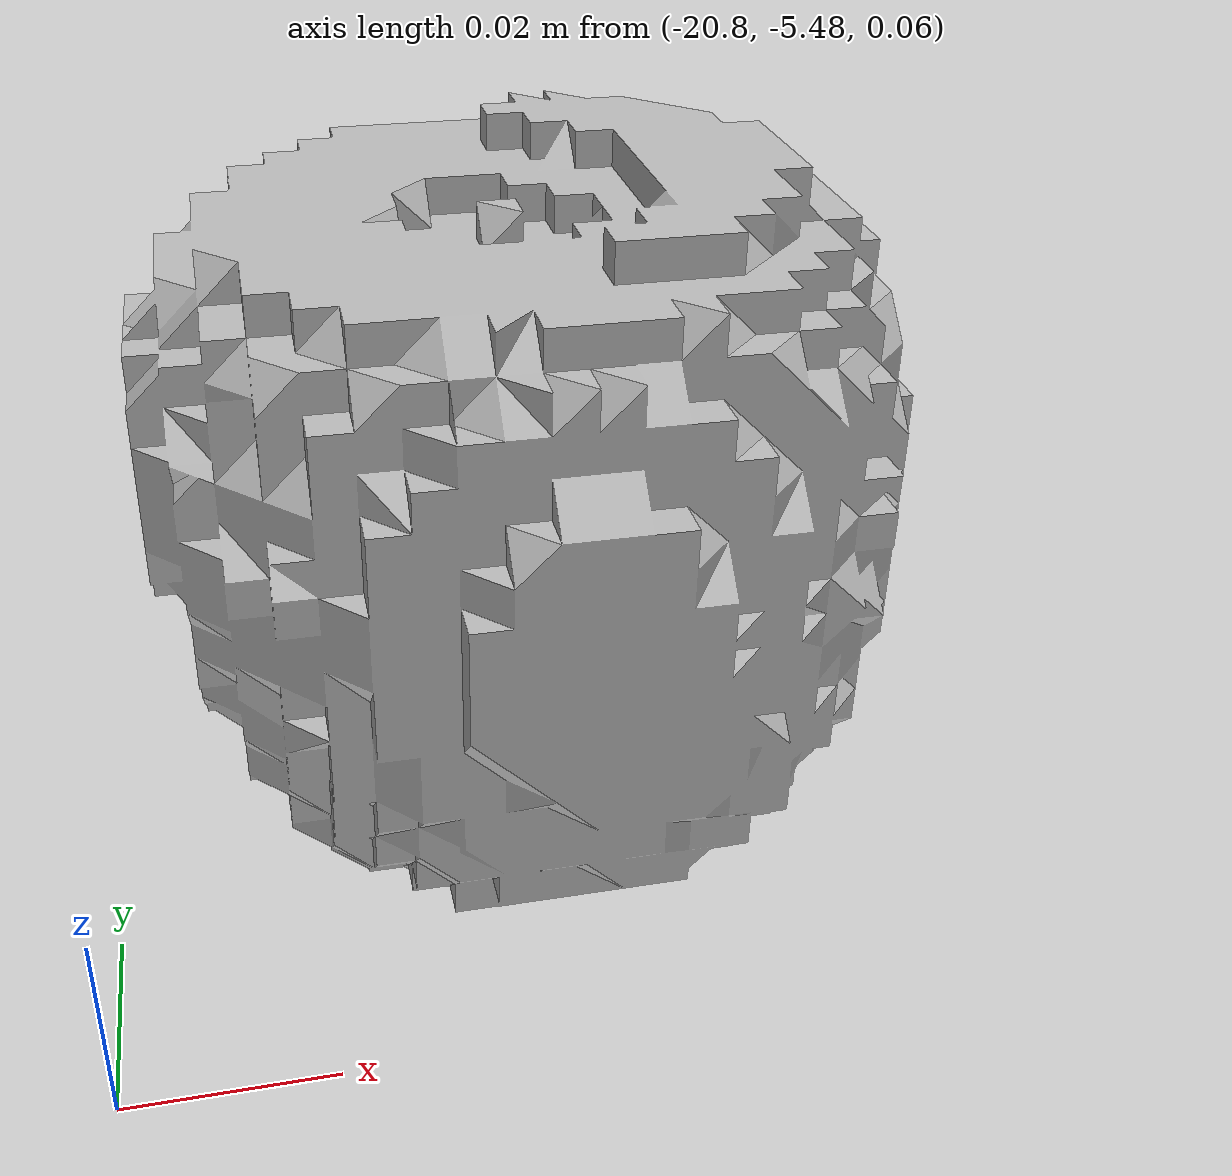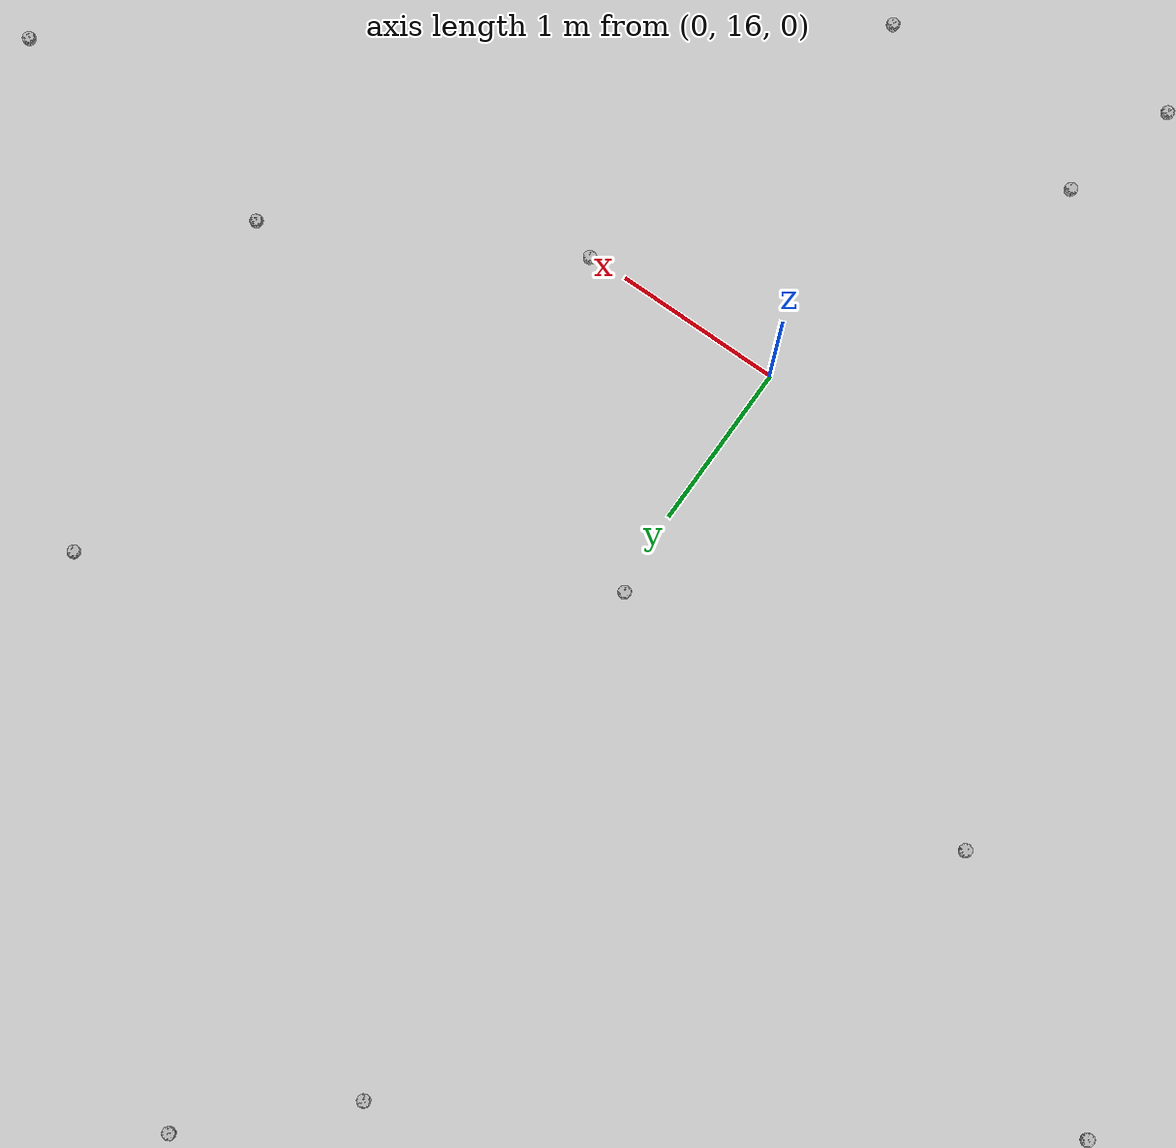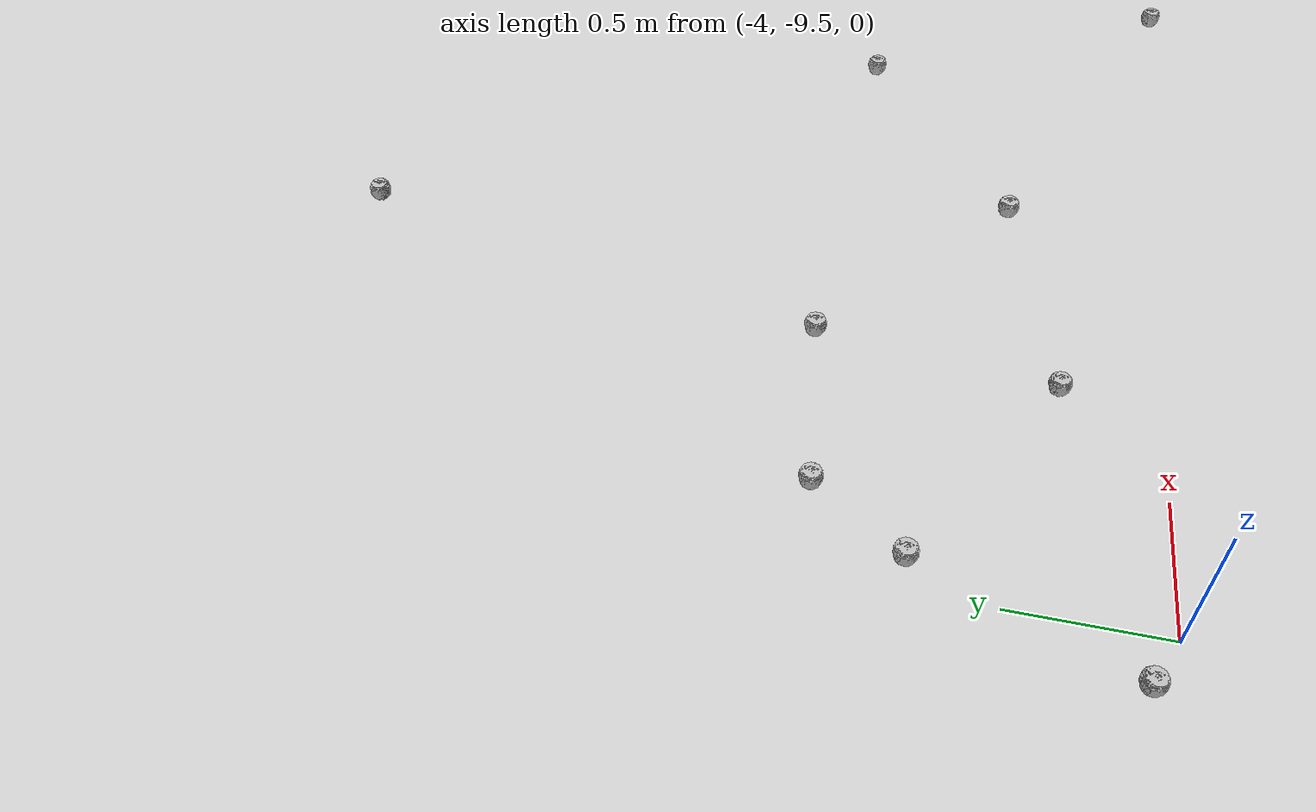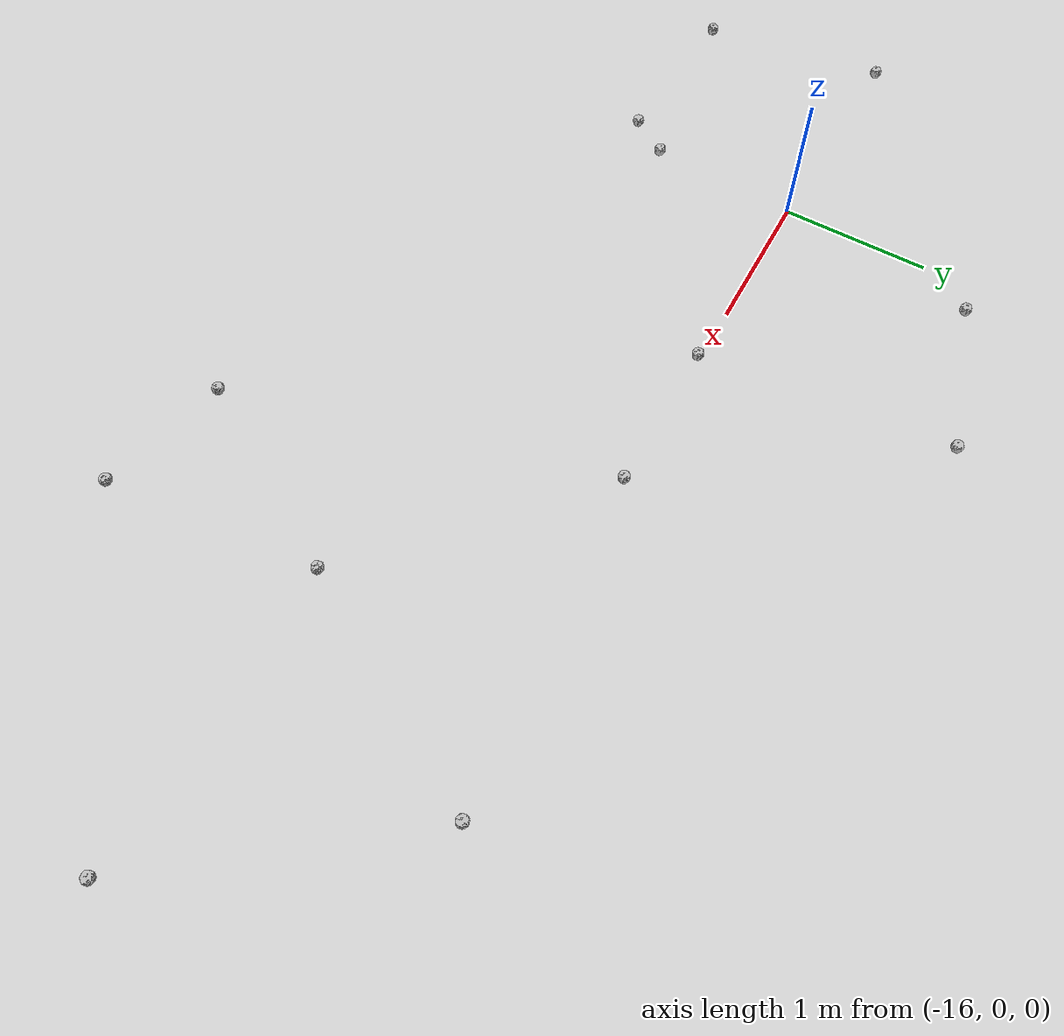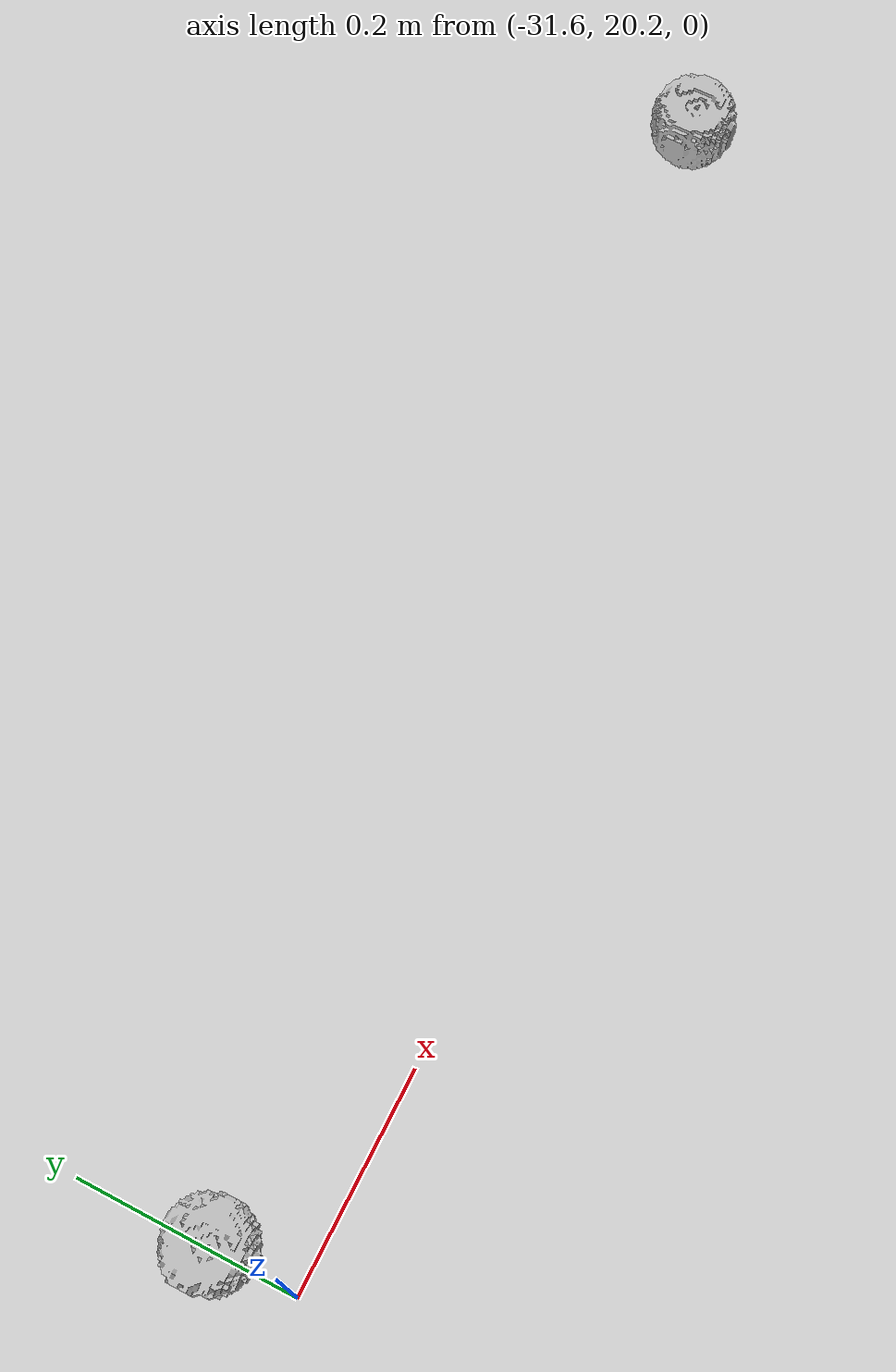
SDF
<sdf version="1.7">
 <world name="empty_world">
  <spherical_coordinates>
   <surface_model>EARTH_WGS84</surface_model>
   <latitude_deg>36.7668811</latitude_deg>
   <longitude_deg>127.2816851</longitude_deg>
   <elevation>488.0</elevation>
   <heading_deg>180</heading_deg>
  </spherical_coordinates>
  <model name="ground_plane">
   <static>1</static>
   <link name="link">
    <collision name="collision">
     <geometry><plane><normal>0 0 1</normal><size>1 1</size></plane></geometry>
    </collision>
    <visual name="visual">
     <geometry><plane><normal>0 0 1</normal><size>100 100</size></plane></geometry>
     <material>
      <ambient>0.8 0.8 0.8 1</ambient>
      <diffuse>0.8 0.8 0.8 1</diffuse>
      <specular>0.8 0.8 0.8 1</specular>
     </material>
    </visual>
   </link>
  </model>
  <plugin name="gazebo_ros_state" filename="libgazebo_ros_state.so">
   <ros>
    <namespace>/world</namespace>
    <argument>model_states:=model_states_world</argument>
    <argument>link_states:=link_states_plug</argument>
   </ros>
   <update_rate>100.0</update_rate>
  </plugin>
  <gravity>0 0 -9.8</gravity>
  <magnetic_field>6e-06 2.3e-05 -4.2e-05</magnetic_field>
  <atmosphere type="adiabatic"/>
  <physics type="ode">
   <max_step_size>0.001</max_step_size>
   <real_time_factor>1</real_time_factor>
   <real_time_update_rate>1000</real_time_update_rate>
  </physics>
  <scene><ambient>0.4 0.4 0.4 1</ambient><background>0.7 0.7 0.7 1</background><shadows>1</shadows></scene>
  <audio><device>default</device></audio>
  <light name="user_directional_light_0" type="directional">
   <pose>-14.4469 9.20329 1 0 -0 0</pose>
   <diffuse>0.5 0.5 0.5 1</diffuse>
   <specular>0.1 0.1 0.1 1</specular>
   <direction>0.1 0.1 -0.9</direction>
   <attenuation>
    <range>20</range>
    <constant>0.5</constant>
    <linear>0.01</linear>
    <quadratic>0.001</quadratic>
   </attenuation>
  </light>
  <light name="user_directional_light_1" type="directional">
   <pose>-10.4744 8.9378 1 0 -0 0</pose>
   <diffuse>0.5 0.5 0.5 1</diffuse>
   <specular>0.1 0.1 0.1 1</specular>
   <direction>0.1 0.1 -0.9</direction>
   <attenuation>
    <range>20</range>
    <constant>0.5</constant>
    <linear>0.01</linear>
    <quadratic>0.001</quadratic>
   </attenuation>
  </light>
  <model name="apple">
   <static>1</static>
   <link name="link">
    <inertial>
     <pose>0 0 0.04 0 -0 0</pose>
     <mass>1e-11</mass>
     <inertia><ixx>0.0001</ixx><ixy>0</ixy><ixz>0</ixz><iyy>0.0001</iyy><iyz>0</iyz><izz>0.0001</izz></inertia>
    </inertial>
    <visual name="visual">
     <geometry><mesh><uri>model://013_apple/google_16k/textured.obj</uri></mesh></geometry>
     <material><script><uri>model://013_apple/apple.material</uri><name>apple</name></script></material>
    </visual>
   </link>
   <pose>-3.09492 -9.1495 0 0 -0 0</pose>
  </model>
  <model name="apple_clone">
   <static>1</static>
   <link name="link">
    <inertial>
     <pose>0 0 0.04 0 -0 0</pose>
     <mass>1e-11</mass>
     <inertia><ixx>0.0001</ixx><ixy>0</ixy><ixz>0</ixz><iyy>0.0001</iyy><iyz>0</iyz><izz>0.0001</izz></inertia>
    </inertial>
    <visual name="visual">
     <geometry><mesh><uri>model://013_apple/google_16k/textured.obj</uri></mesh></geometry>
     <material><script><uri>model://013_apple/apple.material</uri><name>apple</name></script></material>
    </visual>
   </link>
   <pose>-3.05072 -8.30781 0.064794 0 -0 0</pose>
  </model>
  <model name="apple_clone_0">
   <static>1</static>
   <link name="link">
    <inertial>
     <pose>0 0 0.04 0 -0 0</pose>
     <mass>1e-11</mass>
     <inertia><ixx>0.0001</ixx><ixy>0</ixy><ixz>0</ixz><iyy>0.0001</iyy><iyz>0</iyz><izz>0.0001</izz></inertia>
    </inertial>
    <visual name="visual">
     <geometry><mesh><uri>model://013_apple/google_16k/textured.obj</uri></mesh></geometry>
     <material><script><uri>model://013_apple/apple.material</uri><name>apple</name></script></material>
    </visual>
   </link>
   <pose>-3.71197 -8.39271 0.064794 0 -0 0</pose>
  </model>
  <model name="apple_clone_1">
   <static>1</static>
   <link name="link">
    <inertial>
     <pose>0 0 0.04 0 -0 0</pose>
     <mass>1e-11</mass>
     <inertia><ixx>0.0001</ixx><ixy>0</ixy><ixz>0</ixz><iyy>0.0001</iyy><iyz>0</iyz><izz>0.0001</izz></inertia>
    </inertial>
    <visual name="visual">
     <geometry><mesh><uri>model://013_apple/google_16k/textured.obj</uri></mesh></geometry>
     <material><script><uri>model://013_apple/apple.material</uri><name>apple</name></script></material>
    </visual>
   </link>
   <pose>-3.93031 -8.70447 0.064794 0 -0 0</pose>
  </model>
  <model name="apple_clone_2">
   <static>1</static>
   <link name="link">
    <inertial>
     <pose>0 0 0.04 0 -0 0</pose>
     <mass>1e-11</mass>
     <inertia><ixx>0.0001</ixx><ixy>0</ixy><ixz>0</ixz><iyy>0.0001</iyy><iyz>0</iyz><izz>0.0001</izz></inertia>
    </inertial>
    <visual name="visual">
     <geometry><mesh><uri>model://013_apple/google_16k/textured.obj</uri></mesh></geometry>
     <material><script><uri>model://013_apple/apple.material</uri><name>apple</name></script></material>
    </visual>
   </link>
   <pose>-4.2057 -9.39 0.064794 0 -0 0</pose>
  </model>
  <model name="apple_clone_3">
   <static>1</static>
   <link name="link">
    <inertial>
     <pose>0 0 0.04 0 -0 0</pose>
     <mass>1e-11</mass>
     <inertia><ixx>0.0001</ixx><ixy>0</ixy><ixz>0</ixz><iyy>0.0001</iyy><iyz>0</iyz><izz>0.0001</izz></inertia>
    </inertial>
    <visual name="visual">
     <geometry><mesh><uri>model://013_apple/google_16k/textured.obj</uri></mesh></geometry>
     <material><script><uri>model://013_apple/apple.material</uri><name>apple</name></script></material>
    </visual>
   </link>
   <pose>-2.25531 -8.93552 0.064682 0 -0 0</pose>
  </model>
  <model name="apple_clone_3_clone">
   <static>1</static>
   <link name="link">
    <inertial>
     <pose>0 0 0.04 0 -0 0</pose>
     <mass>1e-11</mass>
     <inertia><ixx>0.0001</ixx><ixy>0</ixy><ixz>0</ixz><iyy>0.0001</iyy><iyz>0</iyz><izz>0.0001</izz></inertia>
    </inertial>
    <visual name="visual">
     <geometry><mesh><uri>model://013_apple/google_16k/textured.obj</uri></mesh></geometry>
     <material><script><uri>model://013_apple/apple.material</uri><name>apple</name></script></material>
    </visual>
   </link>
   <pose>-1.36394 -8.33045 0.06 0 -0 0</pose>
  </model>
  <model name="apple_clone_3_clone_0">
   <static>1</static>
   <link name="link">
    <inertial>
     <pose>0 0 0.04 0 -0 0</pose>
     <mass>1e-11</mass>
     <inertia><ixx>0.0001</ixx><ixy>0</ixy><ixz>0</ixz><iyy>0.0001</iyy><iyz>0</iyz><izz>0.0001</izz></inertia>
    </inertial>
    <visual name="visual">
     <geometry><mesh><uri>model://013_apple/google_16k/textured.obj</uri></mesh></geometry>
     <material><script><uri>model://013_apple/apple.material</uri><name>apple</name></script></material>
    </visual>
   </link>
   <pose>-0.692744 -9.52765 0.06 0 -0 0</pose>
  </model>
  <model name="apple_clone_3_clone_1">
   <static>1</static>
   <link name="link">
    <inertial>
     <pose>0 0 0.04 0 -0 0</pose>
     <mass>1e-11</mass>
     <inertia><ixx>0.0001</ixx><ixy>0</ixy><ixz>0</ixz><iyy>0.0001</iyy><iyz>0</iyz><izz>0.0001</izz></inertia>
    </inertial>
    <visual name="visual">
     <geometry><mesh><uri>model://013_apple/google_16k/textured.obj</uri></mesh></geometry>
     <material><script><uri>model://013_apple/apple.material</uri><name>apple</name></script></material>
    </visual>
   </link>
   <pose>0.795409 -8.51075 0.06 0 -0 0</pose>
  </model>
  <model name="apple_clone_3_clone_2">
   <static>1</static>
   <link name="link">
    <inertial>
     <pose>0 0 0.04 0 -0 0</pose>
     <mass>1e-11</mass>
     <inertia><ixx>0.0001</ixx><ixy>0</ixy><ixz>0</ixz><iyy>0.0001</iyy><iyz>0</iyz><izz>0.0001</izz></inertia>
    </inertial>
    <visual name="visual">
     <geometry><mesh><uri>model://013_apple/google_16k/textured.obj</uri></mesh></geometry>
     <material><script><uri>model://013_apple/apple.material</uri><name>apple</name></script></material>
    </visual>
   </link>
   <pose>3.45846 -9.68368 0.06 0 -0 0</pose>
  </model>
  <model name="apple_clone_3_clone_3">
   <static>1</static>
   <link name="link">
    <inertial>
     <pose>0 0 0.04 0 -0 0</pose>
     <mass>1e-11</mass>
     <inertia><ixx>0.0001</ixx><ixy>0</ixy><ixz>0</ixz><iyy>0.0001</iyy><iyz>0</iyz><izz>0.0001</izz></inertia>
    </inertial>
    <visual name="visual">
     <geometry><mesh><uri>model://013_apple/google_16k/textured.obj</uri></mesh></geometry>
     <material><script><uri>model://013_apple/apple.material</uri><name>apple</name></script></material>
    </visual>
   </link>
   <pose>4.03834 -12.3939 0.06 0 -0 0</pose>
  </model>
  <model name="apple_clone_3_clone_4">
   <static>1</static>
   <link name="link">
    <inertial>
     <pose>0 0 0.04 0 -0 0</pose>
     <mass>1e-11</mass>
     <inertia><ixx>0.0001</ixx><ixy>0</ixy><ixz>0</ixz><iyy>0.0001</iyy><iyz>0</iyz><izz>0.0001</izz></inertia>
    </inertial>
    <visual name="visual">
     <geometry><mesh><uri>model://013_apple/google_16k/textured.obj</uri></mesh></geometry>
     <material><script><uri>model://013_apple/apple.material</uri><name>apple</name></script></material>
    </visual>
   </link>
   <pose>2.00316 -9.76875 0.06 0 -0 0</pose>
  </model>
  <model name="apple_clone_3_clone_5">
   <static>1</static>
   <link name="link">
    <inertial>
     <pose>0 0 0.04 0 -0 0</pose>
     <mass>1e-11</mass>
     <inertia><ixx>0.0001</ixx><ixy>0</ixy><ixz>0</ixz><iyy>0.0001</iyy><iyz>0</iyz><izz>0.0001</izz></inertia>
    </inertial>
    <visual name="visual">
     <geometry><mesh><uri>model://013_apple/google_16k/textured.obj</uri></mesh></geometry>
     <material><script><uri>model://013_apple/apple.material</uri><name>apple</name></script></material>
    </visual>
   </link>
   <pose>-0.020484 -11.9662 0.06 0 -0 0</pose>
  </model>
  <model name="apple_clone_3_clone_6">
   <static>1</static>
   <link name="link">
    <inertial>
     <pose>0 0 0.04 0 -0 0</pose>
     <mass>1e-11</mass>
     <inertia><ixx>0.0001</ixx><ixy>0</ixy><ixz>0</ixz><iyy>0.0001</iyy><iyz>0</iyz><izz>0.0001</izz></inertia>
    </inertial>
    <visual name="visual">
     <geometry><mesh><uri>model://013_apple/google_16k/textured.obj</uri></mesh></geometry>
     <material><script><uri>model://013_apple/apple.material</uri><name>apple</name></script></material>
    </visual>
   </link>
   <pose>-5.04749 -11.2013 0.06 0 -0 0</pose>
  </model>
  <model name="apple_clone_3_clone_7">
   <static>1</static>
   <link name="link">
    <inertial>
     <pose>0 0 0.04 0 -0 0</pose>
     <mass>1e-11</mass>
     <inertia><ixx>0.0001</ixx><ixy>0</ixy><ixz>0</ixz><iyy>0.0001</iyy><iyz>0</iyz><izz>0.0001</izz></inertia>
    </inertial>
    <visual name="visual">
     <geometry><mesh><uri>model://013_apple/google_16k/textured.obj</uri></mesh></geometry>
     <material><script><uri>model://013_apple/apple.material</uri><name>apple</name></script></material>
    </visual>
   </link>
   <pose>-7.45154 -12.7123 0.06 0 -0 0</pose>
  </model>
  <model name="apple_clone_3_clone_8">
   <static>1</static>
   <link name="link">
    <inertial>
     <pose>0 0 0.04 0 -0 0</pose>
     <mass>1e-11</mass>
     <inertia><ixx>0.0001</ixx><ixy>0</ixy><ixz>0</ixz><iyy>0.0001</iyy><iyz>0</iyz><izz>0.0001</izz></inertia>
    </inertial>
    <visual name="visual">
     <geometry><mesh><uri>model://013_apple/google_16k/textured.obj</uri></mesh></geometry>
     <material><script><uri>model://013_apple/apple.material</uri><name>apple</name></script></material>
    </visual>
   </link>
   <pose>-10.1166 -11.1814 0.06 0 -0 0</pose>
  </model>
  <model name="apple_clone_3_clone_9">
   <static>1</static>
   <link name="link">
    <inertial>
     <pose>0 0 0.04 0 -0 0</pose>
     <mass>1e-11</mass>
     <inertia><ixx>0.0001</ixx><ixy>0</ixy><ixz>0</ixz><iyy>0.0001</iyy><iyz>0</iyz><izz>0.0001</izz></inertia>
    </inertial>
    <visual name="visual">
     <geometry><mesh><uri>model://013_apple/google_16k/textured.obj</uri></mesh></geometry>
     <material><script><uri>model://013_apple/apple.material</uri><name>apple</name></script></material>
    </visual>
   </link>
   <pose>-9.96683 -8.85643 0.06 0 -0 0</pose>
  </model>
  <model name="apple_clone_3_clone_10">
   <static>1</static>
   <link name="link">
    <inertial>
     <pose>0 0 0.04 0 -0 0</pose>
     <mass>1e-11</mass>
     <inertia><ixx>0.0001</ixx><ixy>0</ixy><ixz>0</ixz><iyy>0.0001</iyy><iyz>0</iyz><izz>0.0001</izz></inertia>
    </inertial>
    <visual name="visual">
     <geometry><mesh><uri>model://013_apple/google_16k/textured.obj</uri></mesh></geometry>
     <material><script><uri>model://013_apple/apple.material</uri><name>apple</name></script></material>
    </visual>
   </link>
   <pose>-8.05574 -7.64795 0.06 0 -0 0</pose>
  </model>
  <model name="apple_clone_3_clone_11">
   <static>1</static>
   <link name="link">
    <inertial>
     <pose>0 0 0.04 0 -0 0</pose>
     <mass>1e-11</mass>
     <inertia><ixx>0.0001</ixx><ixy>0</ixy><ixz>0</ixz><iyy>0.0001</iyy><iyz>0</iyz><izz>0.0001</izz></inertia>
    </inertial>
    <visual name="visual">
     <geometry><mesh><uri>model://013_apple/google_16k/textured.obj</uri></mesh></geometry>
     <material><script><uri>model://013_apple/apple.material</uri><name>apple</name></script></material>
    </visual>
   </link>
   <pose>-6.23762 -5.6073 0.06 0 -0 0</pose>
  </model>
  <model name="apple_clone_3_clone_12">
   <static>1</static>
   <link name="link">
    <inertial>
     <pose>0 0 0.04 0 -0 0</pose>
     <mass>1e-11</mass>
     <inertia><ixx>0.0001</ixx><ixy>0</ixy><ixz>0</ixz><iyy>0.0001</iyy><iyz>0</iyz><izz>0.0001</izz></inertia>
    </inertial>
    <visual name="visual">
     <geometry><mesh><uri>model://013_apple/google_16k/textured.obj</uri></mesh></geometry>
     <material><script><uri>model://013_apple/apple.material</uri><name>apple</name></script></material>
    </visual>
   </link>
   <pose>-0.477624 -4.77475 0.06 0 -0 0</pose>
  </model>
  <model name="apple_clone_3_clone_13">
   <static>1</static>
   <link name="link">
    <inertial>
     <pose>0 0 0.04 0 -0 0</pose>
     <mass>1e-11</mass>
     <inertia><ixx>0.0001</ixx><ixy>0</ixy><ixz>0</ixz><iyy>0.0001</iyy><iyz>0</iyz><izz>0.0001</izz></inertia>
    </inertial>
    <visual name="visual">
     <geometry><mesh><uri>model://013_apple/google_16k/textured.obj</uri></mesh></geometry>
     <material><script><uri>model://013_apple/apple.material</uri><name>apple</name></script></material>
    </visual>
   </link>
   <pose>3.50331 -5.19015 0.06 0 -0 0</pose>
  </model>
  <model name="apple_clone_3_clone_14">
   <static>1</static>
   <link name="link">
    <inertial>
     <pose>0 0 0.04 0 -0 0</pose>
     <mass>1e-11</mass>
     <inertia><ixx>0.0001</ixx><ixy>0</ixy><ixz>0</ixz><iyy>0.0001</iyy><iyz>0</iyz><izz>0.0001</izz></inertia>
    </inertial>
    <visual name="visual">
     <geometry><mesh><uri>model://013_apple/google_16k/textured.obj</uri></mesh></geometry>
     <material><script><uri>model://013_apple/apple.material</uri><name>apple</name></script></material>
    </visual>
   </link>
   <pose>-2.65589 -6.53614 0.06 0 -0 0</pose>
  </model>
  <model name="apple_clone_3_clone_15">
   <static>1</static>
   <link name="link">
    <inertial>
     <pose>0 0 0.04 0 -0 0</pose>
     <mass>1e-11</mass>
     <inertia><ixx>0.0001</ixx><ixy>0</ixy><ixz>0</ixz><iyy>0.0001</iyy><iyz>0</iyz><izz>0.0001</izz></inertia>
    </inertial>
    <visual name="visual">
     <geometry><mesh><uri>model://013_apple/google_16k/textured.obj</uri></mesh></geometry>
     <material><script><uri>model://013_apple/apple.material</uri><name>apple</name></script></material>
    </visual>
   </link>
   <pose>-6.99762 -9.68019 0.06 0 -0 0</pose>
  </model>
  <model name="apple_clone_3_clone_16">
   <static>1</static>
   <link name="link">
    <inertial>
     <pose>0 0 0.04 0 -0 0</pose>
     <mass>1e-11</mass>
     <inertia><ixx>0.0001</ixx><ixy>0</ixy><ixz>0</ixz><iyy>0.0001</iyy><iyz>0</iyz><izz>0.0001</izz></inertia>
    </inertial>
    <visual name="visual">
     <geometry><mesh><uri>model://013_apple/google_16k/textured.obj</uri></mesh></geometry>
     <material><script><uri>model://013_apple/apple.material</uri><name>apple</name></script></material>
    </visual>
   </link>
   <pose>-3.12104 -12.5236 0.06 0 -0 0</pose>
  </model>
  <model name="apple_clone_3_clone_17">
   <static>1</static>
   <link name="link">
    <inertial>
     <pose>0 0 0.04 0 -0 0</pose>
     <mass>1e-11</mass>
     <inertia><ixx>0.0001</ixx><ixy>0</ixy><ixz>0</ixz><iyy>0.0001</iyy><iyz>0</iyz><izz>0.0001</izz></inertia>
    </inertial>
    <visual name="visual">
     <geometry><mesh><uri>model://013_apple/google_16k/textured.obj</uri></mesh></geometry>
     <material><script><uri>model://013_apple/apple.material</uri><name>apple</name></script></material>
    </visual>
   </link>
   <pose>1.77985 -2.9431 0.06 0 -0 0</pose>
  </model>
  <model name="apple_clone_3_clone_18">
   <static>1</static>
   <link name="link">
    <inertial>
     <pose>0 0 0.04 0 -0 0</pose>
     <mass>1e-11</mass>
     <inertia><ixx>0.0001</ixx><ixy>0</ixy><ixz>0</ixz><iyy>0.0001</iyy><iyz>0</iyz><izz>0.0001</izz></inertia>
    </inertial>
    <visual name="visual">
     <geometry><mesh><uri>model://013_apple/google_16k/textured.obj</uri></mesh></geometry>
     <material><script><uri>model://013_apple/apple.material</uri><name>apple</name></script></material>
    </visual>
   </link>
   <pose>-4.29077 -3.04568 0.06 0 -0 0</pose>
  </model>
  <model name="apple_clone_3_clone_19">
   <static>1</static>
   <link name="link">
    <inertial>
     <pose>0 0 0.04 0 -0 0</pose>
     <mass>1e-11</mass>
     <inertia><ixx>0.0001</ixx><ixy>0</ixy><ixz>0</ixz><iyy>0.0001</iyy><iyz>0</iyz><izz>0.0001</izz></inertia>
    </inertial>
    <visual name="visual">
     <geometry><mesh><uri>model://013_apple/google_16k/textured.obj</uri></mesh></geometry>
     <material><script><uri>model://013_apple/apple.material</uri><name>apple</name></script></material>
    </visual>
   </link>
   <pose>-6.10808 -0.325178 0.06 0 -0 0</pose>
  </model>
  <model name="apple_clone_3_clone_20">
   <static>1</static>
   <link name="link">
    <inertial>
     <pose>0 0 0.04 0 -0 0</pose>
     <mass>1e-11</mass>
     <inertia><ixx>0.0001</ixx><ixy>0</ixy><ixz>0</ixz><iyy>0.0001</iyy><iyz>0</iyz><izz>0.0001</izz></inertia>
    </inertial>
    <visual name="visual">
     <geometry><mesh><uri>model://013_apple/google_16k/textured.obj</uri></mesh></geometry>
     <material><script><uri>model://013_apple/apple.material</uri><name>apple</name></script></material>
    </visual>
   </link>
   <pose>-3.50012 -0.550027 0.06 0 -0 0</pose>
  </model>
  <model name="apple_clone_3_clone_21">
   <static>1</static>
   <link name="link">
    <inertial>
     <pose>0 0 0.04 0 -0 0</pose>
     <mass>1e-11</mass>
     <inertia><ixx>0.0001</ixx><ixy>0</ixy><ixz>0</ixz><iyy>0.0001</iyy><iyz>0</iyz><izz>0.0001</izz></inertia>
    </inertial>
    <visual name="visual">
     <geometry><mesh><uri>model://013_apple/google_16k/textured.obj</uri></mesh></geometry>
     <material><script><uri>model://013_apple/apple.material</uri><name>apple</name></script></material>
    </visual>
   </link>
   <pose>-7.98609 -3.54874 0.06 0 -0 0</pose>
  </model>
  <model name="apple_clone_3_clone_22">
   <static>1</static>
   <link name="link">
    <inertial>
     <pose>0 0 0.04 0 -0 0</pose>
     <mass>1e-11</mass>
     <inertia><ixx>0.0001</ixx><ixy>0</ixy><ixz>0</ixz><iyy>0.0001</iyy><iyz>0</iyz><izz>0.0001</izz></inertia>
    </inertial>
    <visual name="visual">
     <geometry><mesh><uri>model://013_apple/google_16k/textured.obj</uri></mesh></geometry>
     <material><script><uri>model://013_apple/apple.material</uri><name>apple</name></script></material>
    </visual>
   </link>
   <pose>-6.87535 0.867692 0.06 0 -0 0</pose>
  </model>
  <model name="apple_clone_3_clone_23">
   <static>1</static>
   <link name="link">
    <inertial>
     <pose>0 0 0.04 0 -0 0</pose>
     <mass>1e-11</mass>
     <inertia><ixx>0.0001</ixx><ixy>0</ixy><ixz>0</ixz><iyy>0.0001</iyy><iyz>0</iyz><izz>0.0001</izz></inertia>
    </inertial>
    <visual name="visual">
     <geometry><mesh><uri>model://013_apple/google_16k/textured.obj</uri></mesh></geometry>
     <material><script><uri>model://013_apple/apple.material</uri><name>apple</name></script></material>
    </visual>
   </link>
   <pose>-2.58525 -0.427757 0.06 0 -0 0</pose>
  </model>
  <model name="apple_clone_3_clone_24">
   <static>1</static>
   <link name="link">
    <inertial>
     <pose>0 0 0.04 0 -0 0</pose>
     <mass>1e-11</mass>
     <inertia><ixx>0.0001</ixx><ixy>0</ixy><ixz>0</ixz><iyy>0.0001</iyy><iyz>0</iyz><izz>0.0001</izz></inertia>
    </inertial>
    <visual name="visual">
     <geometry><mesh><uri>model://013_apple/google_16k/textured.obj</uri></mesh></geometry>
     <material><script><uri>model://013_apple/apple.material</uri><name>apple</name></script></material>
    </visual>
   </link>
   <pose>1.88612 -2.25308 0.06 0 -0 0</pose>
  </model>
  <model name="apple_clone_3_clone_25">
   <static>1</static>
   <link name="link">
    <inertial>
     <pose>0 0 0.04 0 -0 0</pose>
     <mass>1e-11</mass>
     <inertia><ixx>0.0001</ixx><ixy>0</ixy><ixz>0</ixz><iyy>0.0001</iyy><iyz>0</iyz><izz>0.0001</izz></inertia>
    </inertial>
    <visual name="visual">
     <geometry><mesh><uri>model://013_apple/google_16k/textured.obj</uri></mesh></geometry>
     <material><script><uri>model://013_apple/apple.material</uri><name>apple</name></script></material>
    </visual>
   </link>
   <pose>3.77385 0.433579 0.06 0 -0 0</pose>
  </model>
  <model name="apple_clone_3_clone_26">
   <static>1</static>
   <link name="link">
    <inertial>
     <pose>0 0 0.04 0 -0 0</pose>
     <mass>1e-11</mass>
     <inertia><ixx>0.0001</ixx><ixy>0</ixy><ixz>0</ixz><iyy>0.0001</iyy><iyz>0</iyz><izz>0.0001</izz></inertia>
    </inertial>
    <visual name="visual">
     <geometry><mesh><uri>model://013_apple/google_16k/textured.obj</uri></mesh></geometry>
     <material><script><uri>model://013_apple/apple.material</uri><name>apple</name></script></material>
    </visual>
   </link>
   <pose>2.51538 1.51788 0.06 0 -0 0</pose>
  </model>
  <model name="apple_clone_3_clone_27">
   <static>1</static>
   <link name="link">
    <inertial>
     <pose>0 0 0.04 0 -0 0</pose>
     <mass>1e-11</mass>
     <inertia><ixx>0.0001</ixx><ixy>0</ixy><ixz>0</ixz><iyy>0.0001</iyy><iyz>0</iyz><izz>0.0001</izz></inertia>
    </inertial>
    <visual name="visual">
     <geometry><mesh><uri>model://013_apple/google_16k/textured.obj</uri></mesh></geometry>
     <material><script><uri>model://013_apple/apple.material</uri><name>apple</name></script></material>
    </visual>
   </link>
   <pose>-1.12669 -3.09949 0.06 0 -0 0</pose>
  </model>
  <model name="apple_clone_3_clone_28">
   <static>1</static>
   <link name="link">
    <inertial>
     <pose>0 0 0.04 0 -0 0</pose>
     <mass>1e-11</mass>
     <inertia><ixx>0.0001</ixx><ixy>0</ixy><ixz>0</ixz><iyy>0.0001</iyy><iyz>0</iyz><izz>0.0001</izz></inertia>
    </inertial>
    <visual name="visual">
     <geometry><mesh><uri>model://013_apple/google_16k/textured.obj</uri></mesh></geometry>
     <material><script><uri>model://013_apple/apple.material</uri><name>apple</name></script></material>
    </visual>
   </link>
   <pose>-6.05414 -3.61378 0.06 0 -0 0</pose>
  </model>
  <model name="apple_clone_3_clone_29">
   <static>1</static>
   <link name="link">
    <inertial>
     <pose>0 0 0.04 0 -0 0</pose>
     <mass>1e-11</mass>
     <inertia><ixx>0.0001</ixx><ixy>0</ixy><ixz>0</ixz><iyy>0.0001</iyy><iyz>0</iyz><izz>0.0001</izz></inertia>
    </inertial>
    <visual name="visual">
     <geometry><mesh><uri>model://013_apple/google_16k/textured.obj</uri></mesh></geometry>
     <material><script><uri>model://013_apple/apple.material</uri><name>apple</name></script></material>
    </visual>
   </link>
   <pose>-10.1395 -2.07378 0.06 0 -0 0</pose>
  </model>
  <model name="apple_clone_3_clone_30">
   <static>1</static>
   <link name="link">
    <inertial>
     <pose>0 0 0.04 0 -0 0</pose>
     <mass>1e-11</mass>
     <inertia><ixx>0.0001</ixx><ixy>0</ixy><ixz>0</ixz><iyy>0.0001</iyy><iyz>0</iyz><izz>0.0001</izz></inertia>
    </inertial>
    <visual name="visual">
     <geometry><mesh><uri>model://013_apple/google_16k/textured.obj</uri></mesh></geometry>
     <material><script><uri>model://013_apple/apple.material</uri><name>apple</name></script></material>
    </visual>
   </link>
   <pose>-13.5087 -5.74073 0.06 0 -0 0</pose>
  </model>
  <model name="apple_clone_3_clone_31">
   <static>1</static>
   <link name="link">
    <inertial>
     <pose>0 0 0.04 0 -0 0</pose>
     <mass>1e-11</mass>
     <inertia><ixx>0.0001</ixx><ixy>0</ixy><ixz>0</ixz><iyy>0.0001</iyy><iyz>0</iyz><izz>0.0001</izz></inertia>
    </inertial>
    <visual name="visual">
     <geometry><mesh><uri>model://013_apple/google_16k/textured.obj</uri></mesh></geometry>
     <material><script><uri>model://013_apple/apple.material</uri><name>apple</name></script></material>
    </visual>
   </link>
   <pose>-12.8664 -2.51974 0.06 0 -0 0</pose>
  </model>
  <model name="apple_clone_3_clone_32">
   <static>1</static>
   <link name="link">
    <inertial>
     <pose>0 0 0.04 0 -0 0</pose>
     <mass>1e-11</mass>
     <inertia><ixx>0.0001</ixx><ixy>0</ixy><ixz>0</ixz><iyy>0.0001</iyy><iyz>0</iyz><izz>0.0001</izz></inertia>
    </inertial>
    <visual name="visual">
     <geometry><mesh><uri>model://013_apple/google_16k/textured.obj</uri></mesh></geometry>
     <material><script><uri>model://013_apple/apple.material</uri><name>apple</name></script></material>
    </visual>
   </link>
   <pose>-12.1713 -1.27165 0.06 0 -0 0</pose>
  </model>
  <model name="apple_clone_3_clone_33">
   <static>1</static>
   <link name="link">
    <inertial>
     <pose>0 0 0.04 0 -0 0</pose>
     <mass>1e-11</mass>
     <inertia><ixx>0.0001</ixx><ixy>0</ixy><ixz>0</ixz><iyy>0.0001</iyy><iyz>0</iyz><izz>0.0001</izz></inertia>
    </inertial>
    <visual name="visual">
     <geometry><mesh><uri>model://013_apple/google_16k/textured.obj</uri></mesh></geometry>
     <material><script><uri>model://013_apple/apple.material</uri><name>apple</name></script></material>
    </visual>
   </link>
   <pose>-13.5569 0 0.06 0 -0 0</pose>
  </model>
  <model name="apple_clone_3_clone_34">
   <static>1</static>
   <link name="link">
    <inertial>
     <pose>0 0 0.04 0 -0 0</pose>
     <mass>1e-11</mass>
     <inertia><ixx>0.0001</ixx><ixy>0</ixy><ixz>0</ixz><iyy>0.0001</iyy><iyz>0</iyz><izz>0.0001</izz></inertia>
    </inertial>
    <visual name="visual">
     <geometry><mesh><uri>model://013_apple/google_16k/textured.obj</uri></mesh></geometry>
     <material><script><uri>model://013_apple/apple.material</uri><name>apple</name></script></material>
    </visual>
   </link>
   <pose>-11.3686 0.206724 0.06 0 -0 0</pose>
  </model>
  <model name="apple_clone_3_clone_35">
   <static>1</static>
   <link name="link">
    <inertial>
     <pose>0 0 0.04 0 -0 0</pose>
     <mass>1e-11</mass>
     <inertia><ixx>0.0001</ixx><ixy>0</ixy><ixz>0</ixz><iyy>0.0001</iyy><iyz>0</iyz><izz>0.0001</izz></inertia>
    </inertial>
    <visual name="visual">
     <geometry><mesh><uri>model://013_apple/google_16k/textured.obj</uri></mesh></geometry>
     <material><script><uri>model://013_apple/apple.material</uri><name>apple</name></script></material>
    </visual>
   </link>
   <pose>-14.5707 0 0.06 0 -0 0</pose>
  </model>
  <model name="apple_clone_3_clone_36">
   <static>1</static>
   <link name="link">
    <inertial>
     <pose>0 0 0.04 0 -0 0</pose>
     <mass>1e-11</mass>
     <inertia><ixx>0.0001</ixx><ixy>0</ixy><ixz>0</ixz><iyy>0.0001</iyy><iyz>0</iyz><izz>0.0001</izz></inertia>
    </inertial>
    <visual name="visual">
     <geometry><mesh><uri>model://013_apple/google_16k/textured.obj</uri></mesh></geometry>
     <material><script><uri>model://013_apple/apple.material</uri><name>apple</name></script></material>
    </visual>
   </link>
   <pose>-16.1719 -1.26165 0.06 0 -0 0</pose>
  </model>
  <model name="apple_clone_3_clone_37">
   <static>1</static>
   <link name="link">
    <inertial>
     <pose>0 0 0.04 0 -0 0</pose>
     <mass>1e-11</mass>
     <inertia><ixx>0.0001</ixx><ixy>0</ixy><ixz>0</ixz><iyy>0.0001</iyy><iyz>0</iyz><izz>0.0001</izz></inertia>
    </inertial>
    <visual name="visual">
     <geometry><mesh><uri>model://013_apple/google_16k/textured.obj</uri></mesh></geometry>
     <material><script><uri>model://013_apple/apple.material</uri><name>apple</name></script></material>
    </visual>
   </link>
   <pose>-16.0129 -4.29524 0.06 0 -0 0</pose>
  </model>
  <model name="apple_clone_3_clone_38">
   <static>1</static>
   <link name="link">
    <inertial>
     <pose>0 0 0.04 0 -0 0</pose>
     <mass>1e-11</mass>
     <inertia><ixx>0.0001</ixx><ixy>0</ixy><ixz>0</ixz><iyy>0.0001</iyy><iyz>0</iyz><izz>0.0001</izz></inertia>
    </inertial>
    <visual name="visual">
     <geometry><mesh><uri>model://013_apple/google_16k/textured.obj</uri></mesh></geometry>
     <material><script><uri>model://013_apple/apple.material</uri><name>apple</name></script></material>
    </visual>
   </link>
   <pose>-15.7143 -6.87501 0.06 0 -0 0</pose>
  </model>
  <model name="apple_clone_3_clone_39">
   <static>1</static>
   <link name="link">
    <inertial>
     <pose>0 0 0.04 0 -0 0</pose>
     <mass>1e-11</mass>
     <inertia><ixx>0.0001</ixx><ixy>0</ixy><ixz>0</ixz><iyy>0.0001</iyy><iyz>0</iyz><izz>0.0001</izz></inertia>
    </inertial>
    <visual name="visual">
     <geometry><mesh><uri>model://013_apple/google_16k/textured.obj</uri></mesh></geometry>
     <material><script><uri>model://013_apple/apple.material</uri><name>apple</name></script></material>
    </visual>
   </link>
   <pose>-14.3545 -6.32502 0.06 0 -0 0</pose>
  </model>
  <model name="apple_clone_3_clone_40">
   <static>1</static>
   <link name="link">
    <inertial>
     <pose>0 0 0.04 0 -0 0</pose>
     <mass>1e-11</mass>
     <inertia><ixx>0.0001</ixx><ixy>0</ixy><ixz>0</ixz><iyy>0.0001</iyy><iyz>0</iyz><izz>0.0001</izz></inertia>
    </inertial>
    <visual name="visual">
     <geometry><mesh><uri>model://013_apple/google_16k/textured.obj</uri></mesh></geometry>
     <material><script><uri>model://013_apple/apple.material</uri><name>apple</name></script></material>
    </visual>
   </link>
   <pose>-17 -6 0.06 0 -0 0</pose>
  </model>
  <model name="apple_clone_3_clone_41">
   <static>1</static>
   <link name="link">
    <inertial>
     <pose>0 0 0.04 0 -0 0</pose>
     <mass>1e-11</mass>
     <inertia><ixx>0.0001</ixx><ixy>0</ixy><ixz>0</ixz><iyy>0.0001</iyy><iyz>0</iyz><izz>0.0001</izz></inertia>
    </inertial>
    <visual name="visual">
     <geometry><mesh><uri>model://013_apple/google_16k/textured.obj</uri></mesh></geometry>
     <material><script><uri>model://013_apple/apple.material</uri><name>apple</name></script></material>
    </visual>
   </link>
   <pose>-2.81299 -4.87567 0.06 0 -0 0</pose>
  </model>
  <model name="apple_clone_3_clone_42">
   <static>1</static>
   <link name="link">
    <inertial>
     <pose>0 0 0.04 0 -0 0</pose>
     <mass>1e-11</mass>
     <inertia><ixx>0.0001</ixx><ixy>0</ixy><ixz>0</ixz><iyy>0.0001</iyy><iyz>0</iyz><izz>0.0001</izz></inertia>
    </inertial>
    <visual name="visual">
     <geometry><mesh><uri>model://013_apple/google_16k/textured.obj</uri></mesh></geometry>
     <material><script><uri>model://013_apple/apple.material</uri><name>apple</name></script></material>
    </visual>
   </link>
   <pose>-8.54058 -5.24083 0.06 0 -0 0</pose>
  </model>
  <model name="apple_clone_3_clone_43">
   <static>1</static>
   <link name="link">
    <inertial>
     <pose>0 0 0.04 0 -0 0</pose>
     <mass>1e-11</mass>
     <inertia><ixx>0.0001</ixx><ixy>0</ixy><ixz>0</ixz><iyy>0.0001</iyy><iyz>0</iyz><izz>0.0001</izz></inertia>
    </inertial>
    <visual name="visual">
     <geometry><mesh><uri>model://013_apple/google_16k/textured.obj</uri></mesh></geometry>
     <material><script><uri>model://013_apple/apple.material</uri><name>apple</name></script></material>
    </visual>
   </link>
   <pose>-10.0944 -7.16946 0.06 0 -0 0</pose>
  </model>
  <model name="apple_clone_3_clone_44">
   <static>1</static>
   <link name="link">
    <inertial>
     <pose>0 0 0.04 0 -0 0</pose>
     <mass>1e-11</mass>
     <inertia><ixx>0.0001</ixx><ixy>0</ixy><ixz>0</ixz><iyy>0.0001</iyy><iyz>0</iyz><izz>0.0001</izz></inertia>
    </inertial>
    <visual name="visual">
     <geometry><mesh><uri>model://013_apple/google_16k/textured.obj</uri></mesh></geometry>
     <material><script><uri>model://013_apple/apple.material</uri><name>apple</name></script></material>
    </visual>
   </link>
   <pose>-13.4732 -7.70269 0.06 0 -0 0</pose>
  </model>
  <model name="apple_clone_3_clone_45">
   <static>1</static>
   <link name="link">
    <inertial>
     <pose>0 0 0.04 0 -0 0</pose>
     <mass>1e-11</mass>
     <inertia><ixx>0.0001</ixx><ixy>0</ixy><ixz>0</ixz><iyy>0.0001</iyy><iyz>0</iyz><izz>0.0001</izz></inertia>
    </inertial>
    <visual name="visual">
     <geometry><mesh><uri>model://013_apple/google_16k/textured.obj</uri></mesh></geometry>
     <material><script><uri>model://013_apple/apple.material</uri><name>apple</name></script></material>
    </visual>
   </link>
   <pose>-15.6701 -8.92963 0.06 0 -0 0</pose>
  </model>
  <model name="apple_clone_3_clone_46">
   <static>1</static>
   <link name="link">
    <inertial>
     <pose>0 0 0.04 0 -0 0</pose>
     <mass>1e-11</mass>
     <inertia><ixx>0.0001</ixx><ixy>0</ixy><ixz>0</ixz><iyy>0.0001</iyy><iyz>0</iyz><izz>0.0001</izz></inertia>
    </inertial>
    <visual name="visual">
     <geometry><mesh><uri>model://013_apple/google_16k/textured.obj</uri></mesh></geometry>
     <material><script><uri>model://013_apple/apple.material</uri><name>apple</name></script></material>
    </visual>
   </link>
   <pose>-11.5918 -8.86773 0.06 0 -0 0</pose>
  </model>
  <model name="apple_clone_3_clone_47">
   <static>1</static>
   <link name="link">
    <inertial>
     <pose>0 0 0.04 0 -0 0</pose>
     <mass>1e-11</mass>
     <inertia><ixx>0.0001</ixx><ixy>0</ixy><ixz>0</ixz><iyy>0.0001</iyy><iyz>0</iyz><izz>0.0001</izz></inertia>
    </inertial>
    <visual name="visual">
     <geometry><mesh><uri>model://013_apple/google_16k/textured.obj</uri></mesh></geometry>
     <material><script><uri>model://013_apple/apple.material</uri><name>apple</name></script></material>
    </visual>
   </link>
   <pose>-14 -10 0.06 0 -0 0</pose>
  </model>
  <model name="apple_clone_3_clone_48">
   <static>1</static>
   <link name="link">
    <inertial>
     <pose>0 0 0.04 0 -0 0</pose>
     <mass>1e-11</mass>
     <inertia><ixx>0.0001</ixx><ixy>0</ixy><ixz>0</ixz><iyy>0.0001</iyy><iyz>0</iyz><izz>0.0001</izz></inertia>
    </inertial>
    <visual name="visual">
     <geometry><mesh><uri>model://013_apple/google_16k/textured.obj</uri></mesh></geometry>
     <material><script><uri>model://013_apple/apple.material</uri><name>apple</name></script></material>
    </visual>
   </link>
   <pose>-12.0195 -2.71593 0.06 0 -0 0</pose>
  </model>
  <model name="apple_clone_3_clone_49">
   <static>1</static>
   <link name="link">
    <inertial>
     <pose>0 0 0.04 0 -0 0</pose>
     <mass>1e-11</mass>
     <inertia><ixx>0.0001</ixx><ixy>0</ixy><ixz>0</ixz><iyy>0.0001</iyy><iyz>0</iyz><izz>0.0001</izz></inertia>
    </inertial>
    <visual name="visual">
     <geometry><mesh><uri>model://013_apple/google_16k/textured.obj</uri></mesh></geometry>
     <material><script><uri>model://013_apple/apple.material</uri><name>apple</name></script></material>
    </visual>
   </link>
   <pose>-9.04206 0.45624 0.06 0 -0 0</pose>
  </model>
  <model name="apple_clone_3_clone_50">
   <static>1</static>
   <link name="link">
    <inertial>
     <pose>0 0 0.04 0 -0 0</pose>
     <mass>1e-11</mass>
     <inertia><ixx>0.0001</ixx><ixy>0</ixy><ixz>0</ixz><iyy>0.0001</iyy><iyz>0</iyz><izz>0.0001</izz></inertia>
    </inertial>
    <visual name="visual">
     <geometry><mesh><uri>model://013_apple/google_16k/textured.obj</uri></mesh></geometry>
     <material><script><uri>model://013_apple/apple.material</uri><name>apple</name></script></material>
    </visual>
   </link>
   <pose>-9.91588 1.66316 0.06 0 -0 0</pose>
  </model>
  <model name="apple_clone_3_clone_51">
   <static>1</static>
   <link name="link">
    <inertial>
     <pose>0 0 0.04 0 -0 0</pose>
     <mass>1e-11</mass>
     <inertia><ixx>0.0001</ixx><ixy>0</ixy><ixz>0</ixz><iyy>0.0001</iyy><iyz>0</iyz><izz>0.0001</izz></inertia>
    </inertial>
    <visual name="visual">
     <geometry><mesh><uri>model://013_apple/google_16k/textured.obj</uri></mesh></geometry>
     <material><script><uri>model://013_apple/apple.material</uri><name>apple</name></script></material>
    </visual>
   </link>
   <pose>-10.2046 -1.30556 0.06 0 -0 0</pose>
  </model>
  <model name="apple_clone_3_clone_52">
   <static>1</static>
   <link name="link">
    <inertial>
     <pose>0 0 0.04 0 -0 0</pose>
     <mass>1e-11</mass>
     <inertia><ixx>0.0001</ixx><ixy>0</ixy><ixz>0</ixz><iyy>0.0001</iyy><iyz>0</iyz><izz>0.0001</izz></inertia>
    </inertial>
    <visual name="visual">
     <geometry><mesh><uri>model://013_apple/google_16k/textured.obj</uri></mesh></geometry>
     <material><script><uri>model://013_apple/apple.material</uri><name>apple</name></script></material>
    </visual>
   </link>
   <pose>-8.04104 -0.239517 0.06 0 -0 0</pose>
  </model>
  <model name="apple_clone_3_clone_53">
   <static>1</static>
   <link name="link">
    <inertial>
     <pose>0 0 0.04 0 -0 0</pose>
     <mass>1e-11</mass>
     <inertia><ixx>0.0001</ixx><ixy>0</ixy><ixz>0</ixz><iyy>0.0001</iyy><iyz>0</iyz><izz>0.0001</izz></inertia>
    </inertial>
    <visual name="visual">
     <geometry><mesh><uri>model://013_apple/google_16k/textured.obj</uri></mesh></geometry>
     <material><script><uri>model://013_apple/apple.material</uri><name>apple</name></script></material>
    </visual>
   </link>
   <pose>-2.83303 3.82556 0.06 0 -0 0</pose>
  </model>
  <model name="apple_clone_3_clone_54">
   <static>1</static>
   <link name="link">
    <inertial>
     <pose>0 0 0.04 0 -0 0</pose>
     <mass>1e-11</mass>
     <inertia><ixx>0.0001</ixx><ixy>0</ixy><ixz>0</ixz><iyy>0.0001</iyy><iyz>0</iyz><izz>0.0001</izz></inertia>
    </inertial>
    <visual name="visual">
     <geometry><mesh><uri>model://013_apple/google_16k/textured.obj</uri></mesh></geometry>
     <material><script><uri>model://013_apple/apple.material</uri><name>apple</name></script></material>
    </visual>
   </link>
   <pose>-4 4 0.06 0 -0 0</pose>
  </model>
  <model name="apple_clone_3_clone_55">
   <static>1</static>
   <link name="link">
    <inertial>
     <pose>0 0 0.04 0 -0 0</pose>
     <mass>1e-11</mass>
     <inertia><ixx>0.0001</ixx><ixy>0</ixy><ixz>0</ixz><iyy>0.0001</iyy><iyz>0</iyz><izz>0.0001</izz></inertia>
    </inertial>
    <visual name="visual">
     <geometry><mesh><uri>model://013_apple/google_16k/textured.obj</uri></mesh></geometry>
     <material><script><uri>model://013_apple/apple.material</uri><name>apple</name></script></material>
    </visual>
   </link>
   <pose>0.240145 2.34996 0.06 0 -0 0</pose>
  </model>
  <model name="apple_clone_3_clone_56">
   <static>1</static>
   <link name="link">
    <inertial>
     <pose>0 0 0.04 0 -0 0</pose>
     <mass>1e-11</mass>
     <inertia><ixx>0.0001</ixx><ixy>0</ixy><ixz>0</ixz><iyy>0.0001</iyy><iyz>0</iyz><izz>0.0001</izz></inertia>
    </inertial>
    <visual name="visual">
     <geometry><mesh><uri>model://013_apple/google_16k/textured.obj</uri></mesh></geometry>
     <material><script><uri>model://013_apple/apple.material</uri><name>apple</name></script></material>
    </visual>
   </link>
   <pose>-1.42106 1.42327 0.06 0 -0 0</pose>
  </model>
  <model name="apple_clone_3_clone_57">
   <static>1</static>
   <link name="link">
    <inertial>
     <pose>0 0 0.04 0 -0 0</pose>
     <mass>1e-11</mass>
     <inertia><ixx>0.0001</ixx><ixy>0</ixy><ixz>0</ixz><iyy>0.0001</iyy><iyz>0</iyz><izz>0.0001</izz></inertia>
    </inertial>
    <visual name="visual">
     <geometry><mesh><uri>model://013_apple/google_16k/textured.obj</uri></mesh></geometry>
     <material><script><uri>model://013_apple/apple.material</uri><name>apple</name></script></material>
    </visual>
   </link>
   <pose>-1.21201 4.65825 0.06 0 -0 0</pose>
  </model>
  <model name="apple_clone_3_clone_58">
   <static>1</static>
   <link name="link">
    <inertial>
     <pose>0 0 0.04 0 -0 0</pose>
     <mass>1e-11</mass>
     <inertia><ixx>0.0001</ixx><ixy>0</ixy><ixz>0</ixz><iyy>0.0001</iyy><iyz>0</iyz><izz>0.0001</izz></inertia>
    </inertial>
    <visual name="visual">
     <geometry><mesh><uri>model://013_apple/google_16k/textured.obj</uri></mesh></geometry>
     <material><script><uri>model://013_apple/apple.material</uri><name>apple</name></script></material>
    </visual>
   </link>
   <pose>0.987 4.85658 0.06 0 -0 0</pose>
  </model>
  <model name="apple_clone_3_clone_59">
   <static>1</static>
   <link name="link">
    <inertial>
     <pose>0 0 0.04 0 -0 0</pose>
     <mass>1e-11</mass>
     <inertia><ixx>0.0001</ixx><ixy>0</ixy><ixz>0</ixz><iyy>0.0001</iyy><iyz>0</iyz><izz>0.0001</izz></inertia>
    </inertial>
    <visual name="visual">
     <geometry><mesh><uri>model://013_apple/google_16k/textured.obj</uri></mesh></geometry>
     <material><script><uri>model://013_apple/apple.material</uri><name>apple</name></script></material>
    </visual>
   </link>
   <pose>2.38866 6.07467 0.06 0 -0 0</pose>
  </model>
  <model name="apple_clone_3_clone_60">
   <static>1</static>
   <link name="link">
    <inertial>
     <pose>0 0 0.04 0 -0 0</pose>
     <mass>1e-11</mass>
     <inertia><ixx>0.0001</ixx><ixy>0</ixy><ixz>0</ixz><iyy>0.0001</iyy><iyz>0</iyz><izz>0.0001</izz></inertia>
    </inertial>
    <visual name="visual">
     <geometry><mesh><uri>model://013_apple/google_16k/textured.obj</uri></mesh></geometry>
     <material><script><uri>model://013_apple/apple.material</uri><name>apple</name></script></material>
    </visual>
   </link>
   <pose>5 5.59309 0.06 0 -0 0</pose>
  </model>
  <model name="apple_clone_3_clone_61">
   <static>1</static>
   <link name="link">
    <inertial>
     <pose>0 0 0.04 0 -0 0</pose>
     <mass>1e-11</mass>
     <inertia><ixx>0.0001</ixx><ixy>0</ixy><ixz>0</ixz><iyy>0.0001</iyy><iyz>0</iyz><izz>0.0001</izz></inertia>
    </inertial>
    <visual name="visual">
     <geometry><mesh><uri>model://013_apple/google_16k/textured.obj</uri></mesh></geometry>
     <material><script><uri>model://013_apple/apple.material</uri><name>apple</name></script></material>
    </visual>
   </link>
   <pose>4.95956 3.00248 0.06 0 -0 0</pose>
  </model>
  <model name="apple_clone_3_clone_62">
   <static>1</static>
   <link name="link">
    <inertial>
     <pose>0 0 0.04 0 -0 0</pose>
     <mass>1e-11</mass>
     <inertia><ixx>0.0001</ixx><ixy>0</ixy><ixz>0</ixz><iyy>0.0001</iyy><iyz>0</iyz><izz>0.0001</izz></inertia>
    </inertial>
    <visual name="visual">
     <geometry><mesh><uri>model://013_apple/google_16k/textured.obj</uri></mesh></geometry>
     <material><script><uri>model://013_apple/apple.material</uri><name>apple</name></script></material>
    </visual>
   </link>
   <pose>-0.467572 5.45248 0.06 0 -0 0</pose>
  </model>
  <model name="apple_clone_3_clone_63">
   <static>1</static>
   <link name="link">
    <inertial>
     <pose>0 0 0.04 0 -0 0</pose>
     <mass>1e-11</mass>
     <inertia><ixx>0.0001</ixx><ixy>0</ixy><ixz>0</ixz><iyy>0.0001</iyy><iyz>0</iyz><izz>0.0001</izz></inertia>
    </inertial>
    <visual name="visual">
     <geometry><mesh><uri>model://013_apple/google_16k/textured.obj</uri></mesh></geometry>
     <material><script><uri>model://013_apple/apple.material</uri><name>apple</name></script></material>
    </visual>
   </link>
   <pose>-2.84201 6.30079 0.06 0 -0 0</pose>
  </model>
  <model name="apple_clone_3_clone_64">
   <static>1</static>
   <link name="link">
    <inertial>
     <pose>0 0 0.04 0 -0 0</pose>
     <mass>1e-11</mass>
     <inertia><ixx>0.0001</ixx><ixy>0</ixy><ixz>0</ixz><iyy>0.0001</iyy><iyz>0</iyz><izz>0.0001</izz></inertia>
    </inertial>
    <visual name="visual">
     <geometry><mesh><uri>model://013_apple/google_16k/textured.obj</uri></mesh></geometry>
     <material><script><uri>model://013_apple/apple.material</uri><name>apple</name></script></material>
    </visual>
   </link>
   <pose>-5.29397 6.81841 0.06 0 -0 0</pose>
  </model>
  <model name="apple_clone_3_clone_65">
   <static>1</static>
   <link name="link">
    <inertial>
     <pose>0 0 0.04 0 -0 0</pose>
     <mass>1e-11</mass>
     <inertia><ixx>0.0001</ixx><ixy>0</ixy><ixz>0</ixz><iyy>0.0001</iyy><iyz>0</iyz><izz>0.0001</izz></inertia>
    </inertial>
    <visual name="visual">
     <geometry><mesh><uri>model://013_apple/google_16k/textured.obj</uri></mesh></geometry>
     <material><script><uri>model://013_apple/apple.material</uri><name>apple</name></script></material>
    </visual>
   </link>
   <pose>-6.91165 4.25154 0.06 0 -0 0</pose>
  </model>
  <model name="apple_clone_3_clone_66">
   <static>1</static>
   <link name="link">
    <inertial>
     <pose>0 0 0.04 0 -0 0</pose>
     <mass>1e-11</mass>
     <inertia><ixx>0.0001</ixx><ixy>0</ixy><ixz>0</ixz><iyy>0.0001</iyy><iyz>0</iyz><izz>0.0001</izz></inertia>
    </inertial>
    <visual name="visual">
     <geometry><mesh><uri>model://013_apple/google_16k/textured.obj</uri></mesh></geometry>
     <material><script><uri>model://013_apple/apple.material</uri><name>apple</name></script></material>
    </visual>
   </link>
   <pose>-5.27149 3.61299 0.06 0 -0 0</pose>
  </model>
  <model name="apple_clone_3_clone_67">
   <static>1</static>
   <link name="link">
    <inertial>
     <pose>0 0 0.04 0 -0 0</pose>
     <mass>1e-11</mass>
     <inertia><ixx>0.0001</ixx><ixy>0</ixy><ixz>0</ixz><iyy>0.0001</iyy><iyz>0</iyz><izz>0.0001</izz></inertia>
    </inertial>
    <visual name="visual">
     <geometry><mesh><uri>model://013_apple/google_16k/textured.obj</uri></mesh></geometry>
     <material><script><uri>model://013_apple/apple.material</uri><name>apple</name></script></material>
    </visual>
   </link>
   <pose>-6.78727 2.49334 0.06 0 -0 0</pose>
  </model>
  <model name="apple_clone_3_clone_68">
   <static>1</static>
   <link name="link">
    <inertial>
     <pose>0 0 0.04 0 -0 0</pose>
     <mass>1e-11</mass>
     <inertia><ixx>0.0001</ixx><ixy>0</ixy><ixz>0</ixz><iyy>0.0001</iyy><iyz>0</iyz><izz>0.0001</izz></inertia>
    </inertial>
    <visual name="visual">
     <geometry><mesh><uri>model://013_apple/google_16k/textured.obj</uri></mesh></geometry>
     <material><script><uri>model://013_apple/apple.material</uri><name>apple</name></script></material>
    </visual>
   </link>
   <pose>-5.36017 1.69971 0.06 0 -0 0</pose>
  </model>
  <model name="apple_clone_3_clone_69">
   <static>1</static>
   <link name="link">
    <inertial>
     <pose>0 0 0.04 0 -0 0</pose>
     <mass>1e-11</mass>
     <inertia><ixx>0.0001</ixx><ixy>0</ixy><ixz>0</ixz><iyy>0.0001</iyy><iyz>0</iyz><izz>0.0001</izz></inertia>
    </inertial>
    <visual name="visual">
     <geometry><mesh><uri>model://013_apple/google_16k/textured.obj</uri></mesh></geometry>
     <material><script><uri>model://013_apple/apple.material</uri><name>apple</name></script></material>
    </visual>
   </link>
   <pose>-8.41988 4.53596 0.06 0 -0 0</pose>
  </model>
  <model name="apple_clone_3_clone_70">
   <static>1</static>
   <link name="link">
    <inertial>
     <pose>0 0 0.04 0 -0 0</pose>
     <mass>1e-11</mass>
     <inertia><ixx>0.0001</ixx><ixy>0</ixy><ixz>0</ixz><iyy>0.0001</iyy><iyz>0</iyz><izz>0.0001</izz></inertia>
    </inertial>
    <visual name="visual">
     <geometry><mesh><uri>model://013_apple/google_16k/textured.obj</uri></mesh></geometry>
     <material><script><uri>model://013_apple/apple.material</uri><name>apple</name></script></material>
    </visual>
   </link>
   <pose>-10.6032 3.4896 0.06 0 -0 0</pose>
  </model>
  <model name="apple_clone_3_clone_71">
   <static>1</static>
   <link name="link">
    <inertial>
     <pose>0 0 0.04 0 -0 0</pose>
     <mass>1e-11</mass>
     <inertia><ixx>0.0001</ixx><ixy>0</ixy><ixz>0</ixz><iyy>0.0001</iyy><iyz>0</iyz><izz>0.0001</izz></inertia>
    </inertial>
    <visual name="visual">
     <geometry><mesh><uri>model://013_apple/google_16k/textured.obj</uri></mesh></geometry>
     <material><script><uri>model://013_apple/apple.material</uri><name>apple</name></script></material>
    </visual>
   </link>
   <pose>-10.7188 5.44143 0.06 0 -0 0</pose>
  </model>
  <model name="apple_clone_3_clone_72">
   <static>1</static>
   <link name="link">
    <inertial>
     <pose>0 0 0.04 0 -0 0</pose>
     <mass>1e-11</mass>
     <inertia><ixx>0.0001</ixx><ixy>0</ixy><ixz>0</ixz><iyy>0.0001</iyy><iyz>0</iyz><izz>0.0001</izz></inertia>
    </inertial>
    <visual name="visual">
     <geometry><mesh><uri>model://013_apple/google_16k/textured.obj</uri></mesh></geometry>
     <material><script><uri>model://013_apple/apple.material</uri><name>apple</name></script></material>
    </visual>
   </link>
   <pose>4.56335 8.27793 0.06 0 -0 0</pose>
  </model>
  <model name="apple_clone_3_clone_73">
   <static>1</static>
   <link name="link">
    <inertial>
     <pose>0 0 0.04 0 -0 0</pose>
     <mass>1e-11</mass>
     <inertia><ixx>0.0001</ixx><ixy>0</ixy><ixz>0</ixz><iyy>0.0001</iyy><iyz>0</iyz><izz>0.0001</izz></inertia>
    </inertial>
    <visual name="visual">
     <geometry><mesh><uri>model://013_apple/google_16k/textured.obj</uri></mesh></geometry>
     <material><script><uri>model://013_apple/apple.material</uri><name>apple</name></script></material>
    </visual>
   </link>
   <pose>3.09138 10.2503 0.06 0 -0 0</pose>
  </model>
  <model name="apple_clone_3_clone_74">
   <static>1</static>
   <link name="link">
    <inertial>
     <pose>0 0 0.04 0 -0 0</pose>
     <mass>1e-11</mass>
     <inertia><ixx>0.0001</ixx><ixy>0</ixy><ixz>0</ixz><iyy>0.0001</iyy><iyz>0</iyz><izz>0.0001</izz></inertia>
    </inertial>
    <visual name="visual">
     <geometry><mesh><uri>model://013_apple/google_16k/textured.obj</uri></mesh></geometry>
     <material><script><uri>model://013_apple/apple.material</uri><name>apple</name></script></material>
    </visual>
   </link>
   <pose>2.2162 8.64602 0.06 0 -0 0</pose>
  </model>
  <model name="apple_clone_3_clone_75">
   <static>1</static>
   <link name="link">
    <inertial>
     <pose>0 0 0.04 0 -0 0</pose>
     <mass>1e-11</mass>
     <inertia><ixx>0.0001</ixx><ixy>0</ixy><ixz>0</ixz><iyy>0.0001</iyy><iyz>0</iyz><izz>0.0001</izz></inertia>
    </inertial>
    <visual name="visual">
     <geometry><mesh><uri>model://013_apple/google_16k/textured.obj</uri></mesh></geometry>
     <material><script><uri>model://013_apple/apple.material</uri><name>apple</name></script></material>
    </visual>
   </link>
   <pose>-0.774713 14.1223 0.06 0 -0 0</pose>
  </model>
  <model name="apple_clone_3_clone_76">
   <static>1</static>
   <link name="link">
    <inertial>
     <pose>0 0 0.04 0 -0 0</pose>
     <mass>1e-11</mass>
     <inertia><ixx>0.0001</ixx><ixy>0</ixy><ixz>0</ixz><iyy>0.0001</iyy><iyz>0</iyz><izz>0.0001</izz></inertia>
    </inertial>
    <visual name="visual">
     <geometry><mesh><uri>model://013_apple/google_16k/textured.obj</uri></mesh></geometry>
     <material><script><uri>model://013_apple/apple.material</uri><name>apple</name></script></material>
    </visual>
   </link>
   <pose>0.589743 12.1273 0.06 0 -0 0</pose>
  </model>
  <model name="apple_clone_3_clone_77">
   <static>1</static>
   <link name="link">
    <inertial>
     <pose>0 0 0.04 0 -0 0</pose>
     <mass>1e-11</mass>
     <inertia><ixx>0.0001</ixx><ixy>0</ixy><ixz>0</ixz><iyy>0.0001</iyy><iyz>0</iyz><izz>0.0001</izz></inertia>
    </inertial>
    <visual name="visual">
     <geometry><mesh><uri>model://013_apple/google_16k/textured.obj</uri></mesh></geometry>
     <material><script><uri>model://013_apple/apple.material</uri><name>apple</name></script></material>
    </visual>
   </link>
   <pose>0.645221 9.04884 0.06 0 -0 0</pose>
  </model>
  <model name="apple_clone_3_clone_78">
   <static>1</static>
   <link name="link">
    <inertial>
     <pose>0 0 0.04 0 -0 0</pose>
     <mass>1e-11</mass>
     <inertia><ixx>0.0001</ixx><ixy>0</ixy><ixz>0</ixz><iyy>0.0001</iyy><iyz>0</iyz><izz>0.0001</izz></inertia>
    </inertial>
    <visual name="visual">
     <geometry><mesh><uri>model://013_apple/google_16k/textured.obj</uri></mesh></geometry>
     <material><script><uri>model://013_apple/apple.material</uri><name>apple</name></script></material>
    </visual>
   </link>
   <pose>-3.05515 12.3709 0.06 0 -0 0</pose>
  </model>
  <model name="apple_clone_3_clone_79">
   <static>1</static>
   <link name="link">
    <inertial>
     <pose>0 0 0.04 0 -0 0</pose>
     <mass>1e-11</mass>
     <inertia><ixx>0.0001</ixx><ixy>0</ixy><ixz>0</ixz><iyy>0.0001</iyy><iyz>0</iyz><izz>0.0001</izz></inertia>
    </inertial>
    <visual name="visual">
     <geometry><mesh><uri>model://013_apple/google_16k/textured.obj</uri></mesh></geometry>
     <material><script><uri>model://013_apple/apple.material</uri><name>apple</name></script></material>
    </visual>
   </link>
   <pose>-3.7662 8.75849 0.06 0 -0 0</pose>
  </model>
  <model name="apple_clone_3_clone_80">
   <static>1</static>
   <link name="link">
    <inertial>
     <pose>0 0 0.04 0 -0 0</pose>
     <mass>1e-11</mass>
     <inertia><ixx>0.0001</ixx><ixy>0</ixy><ixz>0</ixz><iyy>0.0001</iyy><iyz>0</iyz><izz>0.0001</izz></inertia>
    </inertial>
    <visual name="visual">
     <geometry><mesh><uri>model://013_apple/google_16k/textured.obj</uri></mesh></geometry>
     <material><script><uri>model://013_apple/apple.material</uri><name>apple</name></script></material>
    </visual>
   </link>
   <pose>-6.83317 12.4848 0.06 0 -0 0</pose>
  </model>
  <model name="apple_clone_3_clone_81">
   <static>1</static>
   <link name="link">
    <inertial>
     <pose>0 0 0.04 0 -0 0</pose>
     <mass>1e-11</mass>
     <inertia><ixx>0.0001</ixx><ixy>0</ixy><ixz>0</ixz><iyy>0.0001</iyy><iyz>0</iyz><izz>0.0001</izz></inertia>
    </inertial>
    <visual name="visual">
     <geometry><mesh><uri>model://013_apple/google_16k/textured.obj</uri></mesh></geometry>
     <material><script><uri>model://013_apple/apple.material</uri><name>apple</name></script></material>
    </visual>
   </link>
   <pose>-5 13 0.06 0 -0 0</pose>
  </model>
  <model name="apple_clone_3_clone_82">
   <static>1</static>
   <link name="link">
    <inertial>
     <pose>0 0 0.04 0 -0 0</pose>
     <mass>1e-11</mass>
     <inertia><ixx>0.0001</ixx><ixy>0</ixy><ixz>0</ixz><iyy>0.0001</iyy><iyz>0</iyz><izz>0.0001</izz></inertia>
    </inertial>
    <visual name="visual">
     <geometry><mesh><uri>model://013_apple/google_16k/textured.obj</uri></mesh></geometry>
     <material><script><uri>model://013_apple/apple.material</uri><name>apple</name></script></material>
    </visual>
   </link>
   <pose>-5.83861 8.7809 0.06 0 -0 0</pose>
  </model>
  <model name="apple_clone_3_clone_83">
   <static>1</static>
   <link name="link">
    <inertial>
     <pose>0 0 0.04 0 -0 0</pose>
     <mass>1e-11</mass>
     <inertia><ixx>0.0001</ixx><ixy>0</ixy><ixz>0</ixz><iyy>0.0001</iyy><iyz>0</iyz><izz>0.0001</izz></inertia>
    </inertial>
    <visual name="visual">
     <geometry><mesh><uri>model://013_apple/google_16k/textured.obj</uri></mesh></geometry>
     <material><script><uri>model://013_apple/apple.material</uri><name>apple</name></script></material>
    </visual>
   </link>
   <pose>-7.83698 8.35751 0.06 0 -0 0</pose>
  </model>
  <model name="apple_clone_3_clone_84">
   <static>1</static>
   <link name="link">
    <inertial>
     <pose>0 0 0.04 0 -0 0</pose>
     <mass>1e-11</mass>
     <inertia><ixx>0.0001</ixx><ixy>0</ixy><ixz>0</ixz><iyy>0.0001</iyy><iyz>0</iyz><izz>0.0001</izz></inertia>
    </inertial>
    <visual name="visual">
     <geometry><mesh><uri>model://013_apple/google_16k/textured.obj</uri></mesh></geometry>
     <material><script><uri>model://013_apple/apple.material</uri><name>apple</name></script></material>
    </visual>
   </link>
   <pose>-9.6378 14.1152 0.06 0 -0 0</pose>
  </model>
  <model name="apple_clone_3_clone_85">
   <static>1</static>
   <link name="link">
    <inertial>
     <pose>0 0 0.04 0 -0 0</pose>
     <mass>1e-11</mass>
     <inertia><ixx>0.0001</ixx><ixy>0</ixy><ixz>0</ixz><iyy>0.0001</iyy><iyz>0</iyz><izz>0.0001</izz></inertia>
    </inertial>
    <visual name="visual">
     <geometry><mesh><uri>model://013_apple/google_16k/textured.obj</uri></mesh></geometry>
     <material><script><uri>model://013_apple/apple.material</uri><name>apple</name></script></material>
    </visual>
   </link>
   <pose>-13.5578 13.0125 0.06 0 -0 0</pose>
  </model>
  <model name="apple_clone_3_clone_86">
   <static>1</static>
   <link name="link">
    <inertial>
     <pose>0 0 0.04 0 -0 0</pose>
     <mass>1e-11</mass>
     <inertia><ixx>0.0001</ixx><ixy>0</ixy><ixz>0</ixz><iyy>0.0001</iyy><iyz>0</iyz><izz>0.0001</izz></inertia>
    </inertial>
    <visual name="visual">
     <geometry><mesh><uri>model://013_apple/google_16k/textured.obj</uri></mesh></geometry>
     <material><script><uri>model://013_apple/apple.material</uri><name>apple</name></script></material>
    </visual>
   </link>
   <pose>-12.2749 15.4029 0.06 0 -0 0</pose>
  </model>
  <model name="apple_clone_3_clone_87">
   <static>1</static>
   <link name="link">
    <inertial>
     <pose>0 0 0.04 0 -0 0</pose>
     <mass>1e-11</mass>
     <inertia><ixx>0.0001</ixx><ixy>0</ixy><ixz>0</ixz><iyy>0.0001</iyy><iyz>0</iyz><izz>0.0001</izz></inertia>
    </inertial>
    <visual name="visual">
     <geometry><mesh><uri>model://013_apple/google_16k/textured.obj</uri></mesh></geometry>
     <material><script><uri>model://013_apple/apple.material</uri><name>apple</name></script></material>
    </visual>
   </link>
   <pose>-11.4518 10.8777 0.06 0 -0 0</pose>
  </model>
  <model name="apple_clone_3_clone_88">
   <static>1</static>
   <link name="link">
    <inertial>
     <pose>0 0 0.04 0 -0 0</pose>
     <mass>1e-11</mass>
     <inertia><ixx>0.0001</ixx><ixy>0</ixy><ixz>0</ixz><iyy>0.0001</iyy><iyz>0</iyz><izz>0.0001</izz></inertia>
    </inertial>
    <visual name="visual">
     <geometry><mesh><uri>model://013_apple/google_16k/textured.obj</uri></mesh></geometry>
     <material><script><uri>model://013_apple/apple.material</uri><name>apple</name></script></material>
    </visual>
   </link>
   <pose>-15.8561 13.8884 0.06 0 -0 0</pose>
  </model>
  <model name="apple_clone_3_clone_89">
   <static>1</static>
   <link name="link">
    <inertial>
     <pose>0 0 0.04 0 -0 0</pose>
     <mass>1e-11</mass>
     <inertia><ixx>0.0001</ixx><ixy>0</ixy><ixz>0</ixz><iyy>0.0001</iyy><iyz>0</iyz><izz>0.0001</izz></inertia>
    </inertial>
    <visual name="visual">
     <geometry><mesh><uri>model://013_apple/google_16k/textured.obj</uri></mesh></geometry>
     <material><script><uri>model://013_apple/apple.material</uri><name>apple</name></script></material>
    </visual>
   </link>
   <pose>-15.9681 9.73061 0.06 0 -0 0</pose>
  </model>
  <model name="apple_clone_3_clone_90">
   <static>1</static>
   <link name="link">
    <inertial>
     <pose>0 0 0.04 0 -0 0</pose>
     <mass>1e-11</mass>
     <inertia><ixx>0.0001</ixx><ixy>0</ixy><ixz>0</ixz><iyy>0.0001</iyy><iyz>0</iyz><izz>0.0001</izz></inertia>
    </inertial>
    <visual name="visual">
     <geometry><mesh><uri>model://013_apple/google_16k/textured.obj</uri></mesh></geometry>
     <material><script><uri>model://013_apple/apple.material</uri><name>apple</name></script></material>
    </visual>
   </link>
   <pose>-17.964 12.8312 0.06 0 -0 0</pose>
  </model>
  <model name="apple_clone_3_clone_91">
   <static>1</static>
   <link name="link">
    <inertial>
     <pose>0 0 0.04 0 -0 0</pose>
     <mass>1e-11</mass>
     <inertia><ixx>0.0001</ixx><ixy>0</ixy><ixz>0</ixz><iyy>0.0001</iyy><iyz>0</iyz><izz>0.0001</izz></inertia>
    </inertial>
    <visual name="visual">
     <geometry><mesh><uri>model://013_apple/google_16k/textured.obj</uri></mesh></geometry>
     <material><script><uri>model://013_apple/apple.material</uri><name>apple</name></script></material>
    </visual>
   </link>
   <pose>-19.148 8.78549 0.06 0 -0 0</pose>
  </model>
  <model name="apple_clone_3_clone_92">
   <static>1</static>
   <link name="link">
    <inertial>
     <pose>0 0 0.04 0 -0 0</pose>
     <mass>1e-11</mass>
     <inertia><ixx>0.0001</ixx><ixy>0</ixy><ixz>0</ixz><iyy>0.0001</iyy><iyz>0</iyz><izz>0.0001</izz></inertia>
    </inertial>
    <visual name="visual">
     <geometry><mesh><uri>model://013_apple/google_16k/textured.obj</uri></mesh></geometry>
     <material><script><uri>model://013_apple/apple.material</uri><name>apple</name></script></material>
    </visual>
   </link>
   <pose>-8.36519 7.53328 0.06 0 -0 0</pose>
  </model>
  <model name="apple_clone_3_clone_93">
   <static>1</static>
   <link name="link">
    <inertial>
     <pose>0 0 0.04 0 -0 0</pose>
     <mass>1e-11</mass>
     <inertia><ixx>0.0001</ixx><ixy>0</ixy><ixz>0</ixz><iyy>0.0001</iyy><iyz>0</iyz><izz>0.0001</izz></inertia>
    </inertial>
    <visual name="visual">
     <geometry><mesh><uri>model://013_apple/google_16k/textured.obj</uri></mesh></geometry>
     <material><script><uri>model://013_apple/apple.material</uri><name>apple</name></script></material>
    </visual>
   </link>
   <pose>-15.6291 4.71219 0.06 0 -0 0</pose>
  </model>
  <model name="apple_clone_3_clone_94">
   <static>1</static>
   <link name="link">
    <inertial>
     <pose>0 0 0.04 0 -0 0</pose>
     <mass>1e-11</mass>
     <inertia><ixx>0.0001</ixx><ixy>0</ixy><ixz>0</ixz><iyy>0.0001</iyy><iyz>0</iyz><izz>0.0001</izz></inertia>
    </inertial>
    <visual name="visual">
     <geometry><mesh><uri>model://013_apple/google_16k/textured.obj</uri></mesh></geometry>
     <material><script><uri>model://013_apple/apple.material</uri><name>apple</name></script></material>
    </visual>
   </link>
   <pose>-14.4994 6.77098 0.06 0 -0 0</pose>
  </model>
  <model name="apple_clone_3_clone_95">
   <static>1</static>
   <link name="link">
    <inertial>
     <pose>0 0 0.04 0 -0 0</pose>
     <mass>1e-11</mass>
     <inertia><ixx>0.0001</ixx><ixy>0</ixy><ixz>0</ixz><iyy>0.0001</iyy><iyz>0</iyz><izz>0.0001</izz></inertia>
    </inertial>
    <visual name="visual">
     <geometry><mesh><uri>model://013_apple/google_16k/textured.obj</uri></mesh></geometry>
     <material><script><uri>model://013_apple/apple.material</uri><name>apple</name></script></material>
    </visual>
   </link>
   <pose>-14.7373 1.68075 0.06 0 -0 0</pose>
  </model>
  <model name="apple_clone_3_clone_96">
   <static>1</static>
   <link name="link">
    <inertial>
     <pose>0 0 0.04 0 -0 0</pose>
     <mass>1e-11</mass>
     <inertia><ixx>0.0001</ixx><ixy>0</ixy><ixz>0</ixz><iyy>0.0001</iyy><iyz>0</iyz><izz>0.0001</izz></inertia>
    </inertial>
    <visual name="visual">
     <geometry><mesh><uri>model://013_apple/google_16k/textured.obj</uri></mesh></geometry>
     <material><script><uri>model://013_apple/apple.material</uri><name>apple</name></script></material>
    </visual>
   </link>
   <pose>-15.7377 1.37444 0.06 0 -0 0</pose>
  </model>
  <model name="apple_clone_3_clone_97">
   <static>1</static>
   <link name="link">
    <inertial>
     <pose>0 0 0.04 0 -0 0</pose>
     <mass>1e-11</mass>
     <inertia><ixx>0.0001</ixx><ixy>0</ixy><ixz>0</ixz><iyy>0.0001</iyy><iyz>0</iyz><izz>0.0001</izz></inertia>
    </inertial>
    <visual name="visual">
     <geometry><mesh><uri>model://013_apple/google_16k/textured.obj</uri></mesh></geometry>
     <material><script><uri>model://013_apple/apple.material</uri><name>apple</name></script></material>
    </visual>
   </link>
   <pose>-16 -1 0.06 0 -0 0</pose>
  </model>
  <model name="apple_clone_3_clone_98">
   <static>1</static>
   <link name="link">
    <inertial>
     <pose>0 0 0.04 0 -0 0</pose>
     <mass>1e-11</mass>
     <inertia><ixx>0.0001</ixx><ixy>0</ixy><ixz>0</ixz><iyy>0.0001</iyy><iyz>0</iyz><izz>0.0001</izz></inertia>
    </inertial>
    <visual name="visual">
     <geometry><mesh><uri>model://013_apple/google_16k/textured.obj</uri></mesh></geometry>
     <material><script><uri>model://013_apple/apple.material</uri><name>apple</name></script></material>
    </visual>
   </link>
   <pose>-15.7945 3.48756 0.06 0 -0 0</pose>
  </model>
  <model name="apple_clone_3_clone_99">
   <static>1</static>
   <link name="link">
    <inertial>
     <pose>0 0 0.04 0 -0 0</pose>
     <mass>1e-11</mass>
     <inertia><ixx>0.0001</ixx><ixy>0</ixy><ixz>0</ixz><iyy>0.0001</iyy><iyz>0</iyz><izz>0.0001</izz></inertia>
    </inertial>
    <visual name="visual">
     <geometry><mesh><uri>model://013_apple/google_16k/textured.obj</uri></mesh></geometry>
     <material><script><uri>model://013_apple/apple.material</uri><name>apple</name></script></material>
    </visual>
   </link>
   <pose>-8.6621 10.5365 0.06 0 -0 0</pose>
  </model>
  <model name="apple_clone_3_clone_100">
   <static>1</static>
   <link name="link">
    <inertial>
     <pose>0 0 0.04 0 -0 0</pose>
     <mass>1e-11</mass>
     <inertia><ixx>0.0001</ixx><ixy>0</ixy><ixz>0</ixz><iyy>0.0001</iyy><iyz>0</iyz><izz>0.0001</izz></inertia>
    </inertial>
    <visual name="visual">
     <geometry><mesh><uri>model://013_apple/google_16k/textured.obj</uri></mesh></geometry>
     <material><script><uri>model://013_apple/apple.material</uri><name>apple</name></script></material>
    </visual>
   </link>
   <pose>-9.62768 7.74425 0.06 0 -0 0</pose>
  </model>
  <model name="apple_clone_3_clone_101">
   <static>1</static>
   <link name="link">
    <inertial>
     <pose>0 0 0.04 0 -0 0</pose>
     <mass>1e-11</mass>
     <inertia><ixx>0.0001</ixx><ixy>0</ixy><ixz>0</ixz><iyy>0.0001</iyy><iyz>0</iyz><izz>0.0001</izz></inertia>
    </inertial>
    <visual name="visual">
     <geometry><mesh><uri>model://013_apple/google_16k/textured.obj</uri></mesh></geometry>
     <material><script><uri>model://013_apple/apple.material</uri><name>apple</name></script></material>
    </visual>
   </link>
   <pose>-5.60759 15.9379 0.06 0 -0 0</pose>
  </model>
  <model name="apple_clone_3_clone_102">
   <static>1</static>
   <link name="link">
    <inertial>
     <pose>0 0 0.04 0 -0 0</pose>
     <mass>1e-11</mass>
     <inertia><ixx>0.0001</ixx><ixy>0</ixy><ixz>0</ixz><iyy>0.0001</iyy><iyz>0</iyz><izz>0.0001</izz></inertia>
    </inertial>
    <visual name="visual">
     <geometry><mesh><uri>model://013_apple/google_16k/textured.obj</uri></mesh></geometry>
     <material><script><uri>model://013_apple/apple.material</uri><name>apple</name></script></material>
    </visual>
   </link>
   <pose>-6.7041 16.1502 0.06 0 -0 0</pose>
  </model>
  <model name="apple_clone_3_clone_103">
   <static>1</static>
   <link name="link">
    <inertial>
     <pose>0 0 0.04 0 -0 0</pose>
     <mass>1e-11</mass>
     <inertia><ixx>0.0001</ixx><ixy>0</ixy><ixz>0</ixz><iyy>0.0001</iyy><iyz>0</iyz><izz>0.0001</izz></inertia>
    </inertial>
    <visual name="visual">
     <geometry><mesh><uri>model://013_apple/google_16k/textured.obj</uri></mesh></geometry>
     <material><script><uri>model://013_apple/apple.material</uri><name>apple</name></script></material>
    </visual>
   </link>
   <pose>-2.37877 17.6021 0.06 0 -0 0</pose>
  </model>
  <model name="apple_clone_3_clone_104">
   <static>1</static>
   <link name="link">
    <inertial>
     <pose>0 0 0.04 0 -0 0</pose>
     <mass>1e-11</mass>
     <inertia><ixx>0.0001</ixx><ixy>0</ixy><ixz>0</ixz><iyy>0.0001</iyy><iyz>0</iyz><izz>0.0001</izz></inertia>
    </inertial>
    <visual name="visual">
     <geometry><mesh><uri>model://013_apple/google_16k/textured.obj</uri></mesh></geometry>
     <material><script><uri>model://013_apple/apple.material</uri><name>apple</name></script></material>
    </visual>
   </link>
   <pose>-3.8609 15.5497 0.06 0 -0 0</pose>
  </model>
  <model name="apple_clone_3_clone_105">
   <static>1</static>
   <link name="link">
    <inertial>
     <pose>0 0 0.04 0 -0 0</pose>
     <mass>1e-11</mass>
     <inertia><ixx>0.0001</ixx><ixy>0</ixy><ixz>0</ixz><iyy>0.0001</iyy><iyz>0</iyz><izz>0.0001</izz></inertia>
    </inertial>
    <visual name="visual">
     <geometry><mesh><uri>model://013_apple/google_16k/textured.obj</uri></mesh></geometry>
     <material><script><uri>model://013_apple/apple.material</uri><name>apple</name></script></material>
    </visual>
   </link>
   <pose>1.22009 16.0452 0.06 0 -0 0</pose>
  </model>
  <model name="apple_clone_3_clone_106">
   <static>1</static>
   <link name="link">
    <inertial>
     <pose>0 0 0.04 0 -0 0</pose>
     <mass>1e-11</mass>
     <inertia><ixx>0.0001</ixx><ixy>0</ixy><ixz>0</ixz><iyy>0.0001</iyy><iyz>0</iyz><izz>0.0001</izz></inertia>
    </inertial>
    <visual name="visual">
     <geometry><mesh><uri>model://013_apple/google_16k/textured.obj</uri></mesh></geometry>
     <material><script><uri>model://013_apple/apple.material</uri><name>apple</name></script></material>
    </visual>
   </link>
   <pose>0.613888 13.8775 0.06 0 -0 0</pose>
  </model>
  <model name="apple_clone_3_clone_107">
   <static>1</static>
   <link name="link">
    <inertial>
     <pose>0 0 0.04 0 -0 0</pose>
     <mass>1e-11</mass>
     <inertia><ixx>0.0001</ixx><ixy>0</ixy><ixz>0</ixz><iyy>0.0001</iyy><iyz>0</iyz><izz>0.0001</izz></inertia>
    </inertial>
    <visual name="visual">
     <geometry><mesh><uri>model://013_apple/google_16k/textured.obj</uri></mesh></geometry>
     <material><script><uri>model://013_apple/apple.material</uri><name>apple</name></script></material>
    </visual>
   </link>
   <pose>-0.971891 13.4111 0.06 0 -0 0</pose>
  </model>
  <model name="apple_clone_3_clone_108">
   <static>1</static>
   <link name="link">
    <inertial>
     <pose>0 0 0.04 0 -0 0</pose>
     <mass>1e-11</mass>
     <inertia><ixx>0.0001</ixx><ixy>0</ixy><ixz>0</ixz><iyy>0.0001</iyy><iyz>0</iyz><izz>0.0001</izz></inertia>
    </inertial>
    <visual name="visual">
     <geometry><mesh><uri>model://013_apple/google_16k/textured.obj</uri></mesh></geometry>
     <material><script><uri>model://013_apple/apple.material</uri><name>apple</name></script></material>
    </visual>
   </link>
   <pose>5.09102 15.1278 0.06 0 -0 0</pose>
  </model>
  <model name="apple_clone_3_clone_109">
   <static>1</static>
   <link name="link">
    <inertial>
     <pose>0 0 0.04 0 -0 0</pose>
     <mass>1e-11</mass>
     <inertia><ixx>0.0001</ixx><ixy>0</ixy><ixz>0</ixz><iyy>0.0001</iyy><iyz>0</iyz><izz>0.0001</izz></inertia>
    </inertial>
    <visual name="visual">
     <geometry><mesh><uri>model://013_apple/google_16k/textured.obj</uri></mesh></geometry>
     <material><script><uri>model://013_apple/apple.material</uri><name>apple</name></script></material>
    </visual>
   </link>
   <pose>4.38097 12.0424 0.06 0 -0 0</pose>
  </model>
  <model name="apple_clone_3_clone_110">
   <static>1</static>
   <link name="link">
    <inertial>
     <pose>0 0 0.04 0 -0 0</pose>
     <mass>1e-11</mass>
     <inertia><ixx>0.0001</ixx><ixy>0</ixy><ixz>0</ixz><iyy>0.0001</iyy><iyz>0</iyz><izz>0.0001</izz></inertia>
    </inertial>
    <visual name="visual">
     <geometry><mesh><uri>model://013_apple/google_16k/textured.obj</uri></mesh></geometry>
     <material><script><uri>model://013_apple/apple.material</uri><name>apple</name></script></material>
    </visual>
   </link>
   <pose>2.88821 16.9675 0.06 0 -0 0</pose>
  </model>
  <model name="apple_clone_3_clone_111">
   <static>1</static>
   <link name="link">
    <inertial>
     <pose>0 0 0.04 0 -0 0</pose>
     <mass>1e-11</mass>
     <inertia><ixx>0.0001</ixx><ixy>0</ixy><ixz>0</ixz><iyy>0.0001</iyy><iyz>0</iyz><izz>0.0001</izz></inertia>
    </inertial>
    <visual name="visual">
     <geometry><mesh><uri>model://013_apple/google_16k/textured.obj</uri></mesh></geometry>
     <material><script><uri>model://013_apple/apple.material</uri><name>apple</name></script></material>
    </visual>
   </link>
   <pose>4.6266 16.8448 0.06 0 -0 0</pose>
  </model>
  <model name="apple_clone_3_clone_112">
   <static>1</static>
   <link name="link">
    <inertial>
     <pose>0 0 0.04 0 -0 0</pose>
     <mass>1e-11</mass>
     <inertia><ixx>0.0001</ixx><ixy>0</ixy><ixz>0</ixz><iyy>0.0001</iyy><iyz>0</iyz><izz>0.0001</izz></inertia>
    </inertial>
    <visual name="visual">
     <geometry><mesh><uri>model://013_apple/google_16k/textured.obj</uri></mesh></geometry>
     <material><script><uri>model://013_apple/apple.material</uri><name>apple</name></script></material>
    </visual>
   </link>
   <pose>3.00271 13.2972 0.06 0 -0 0</pose>
  </model>
  <model name="apple_clone_3_clone_113">
   <static>1</static>
   <link name="link">
    <inertial>
     <pose>0 0 0.04 0 -0 0</pose>
     <mass>1e-11</mass>
     <inertia><ixx>0.0001</ixx><ixy>0</ixy><ixz>0</ixz><iyy>0.0001</iyy><iyz>0</iyz><izz>0.0001</izz></inertia>
    </inertial>
    <visual name="visual">
     <geometry><mesh><uri>model://013_apple/google_16k/textured.obj</uri></mesh></geometry>
     <material><script><uri>model://013_apple/apple.material</uri><name>apple</name></script></material>
    </visual>
   </link>
   <pose>4.8953 20.4453 0.06 0 -0 0</pose>
  </model>
  <model name="apple_clone_3_clone_114">
   <static>1</static>
   <link name="link">
    <inertial>
     <pose>0 0 0.04 0 -0 0</pose>
     <mass>1e-11</mass>
     <inertia><ixx>0.0001</ixx><ixy>0</ixy><ixz>0</ixz><iyy>0.0001</iyy><iyz>0</iyz><izz>0.0001</izz></inertia>
    </inertial>
    <visual name="visual">
     <geometry><mesh><uri>model://013_apple/google_16k/textured.obj</uri></mesh></geometry>
     <material><script><uri>model://013_apple/apple.material</uri><name>apple</name></script></material>
    </visual>
   </link>
   <pose>2.62161 21.2726 0.06 0 -0 0</pose>
  </model>
  <model name="apple_clone_3_clone_115">
   <static>1</static>
   <link name="link">
    <inertial>
     <pose>0 0 0.04 0 -0 0</pose>
     <mass>1e-11</mass>
     <inertia><ixx>0.0001</ixx><ixy>0</ixy><ixz>0</ixz><iyy>0.0001</iyy><iyz>0</iyz><izz>0.0001</izz></inertia>
    </inertial>
    <visual name="visual">
     <geometry><mesh><uri>model://013_apple/google_16k/textured.obj</uri></mesh></geometry>
     <material><script><uri>model://013_apple/apple.material</uri><name>apple</name></script></material>
    </visual>
   </link>
   <pose>2.54755 19.0901 0.06 0 -0 0</pose>
  </model>
  <model name="apple_clone_3_clone_116">
   <static>1</static>
   <link name="link">
    <inertial>
     <pose>0 0 0.04 0 -0 0</pose>
     <mass>1e-11</mass>
     <inertia><ixx>0.0001</ixx><ixy>0</ixy><ixz>0</ixz><iyy>0.0001</iyy><iyz>0</iyz><izz>0.0001</izz></inertia>
    </inertial>
    <visual name="visual">
     <geometry><mesh><uri>model://013_apple/google_16k/textured.obj</uri></mesh></geometry>
     <material><script><uri>model://013_apple/apple.material</uri><name>apple</name></script></material>
    </visual>
   </link>
   <pose>4.90497 22.8018 0.06 0 -0 0</pose>
  </model>
  <model name="apple_clone_3_clone_117">
   <static>1</static>
   <link name="link">
    <inertial>
     <pose>0 0 0.04 0 -0 0</pose>
     <mass>1e-11</mass>
     <inertia><ixx>0.0001</ixx><ixy>0</ixy><ixz>0</ixz><iyy>0.0001</iyy><iyz>0</iyz><izz>0.0001</izz></inertia>
    </inertial>
    <visual name="visual">
     <geometry><mesh><uri>model://013_apple/google_16k/textured.obj</uri></mesh></geometry>
     <material><script><uri>model://013_apple/apple.material</uri><name>apple</name></script></material>
    </visual>
   </link>
   <pose>3.07039 24.2728 0.06 0 -0 0</pose>
  </model>
  <model name="apple_clone_3_clone_118">
   <static>1</static>
   <link name="link">
    <inertial>
     <pose>0 0 0.04 0 -0 0</pose>
     <mass>1e-11</mass>
     <inertia><ixx>0.0001</ixx><ixy>0</ixy><ixz>0</ixz><iyy>0.0001</iyy><iyz>0</iyz><izz>0.0001</izz></inertia>
    </inertial>
    <visual name="visual">
     <geometry><mesh><uri>model://013_apple/google_16k/textured.obj</uri></mesh></geometry>
     <material><script><uri>model://013_apple/apple.material</uri><name>apple</name></script></material>
    </visual>
   </link>
   <pose>5.05089 25.9336 0.06 0 -0 0</pose>
  </model>
  <model name="apple_clone_3_clone_119">
   <static>1</static>
   <link name="link">
    <inertial>
     <pose>0 0 0.04 0 -0 0</pose>
     <mass>1e-11</mass>
     <inertia><ixx>0.0001</ixx><ixy>0</ixy><ixz>0</ixz><iyy>0.0001</iyy><iyz>0</iyz><izz>0.0001</izz></inertia>
    </inertial>
    <visual name="visual">
     <geometry><mesh><uri>model://013_apple/google_16k/textured.obj</uri></mesh></geometry>
     <material><script><uri>model://013_apple/apple.material</uri><name>apple</name></script></material>
    </visual>
   </link>
   <pose>4.17753 27.6165 0.06 0 -0 0</pose>
  </model>
  <model name="apple_clone_3_clone_120">
   <static>1</static>
   <link name="link">
    <inertial>
     <pose>0 0 0.04 0 -0 0</pose>
     <mass>1e-11</mass>
     <inertia><ixx>0.0001</ixx><ixy>0</ixy><ixz>0</ixz><iyy>0.0001</iyy><iyz>0</iyz><izz>0.0001</izz></inertia>
    </inertial>
    <visual name="visual">
     <geometry><mesh><uri>model://013_apple/google_16k/textured.obj</uri></mesh></geometry>
     <material><script><uri>model://013_apple/apple.material</uri><name>apple</name></script></material>
    </visual>
   </link>
   <pose>0.013751 28.069 0.06 0 -0 0</pose>
  </model>
  <model name="apple_clone_3_clone_121">
   <static>1</static>
   <link name="link">
    <inertial>
     <pose>0 0 0.04 0 -0 0</pose>
     <mass>1e-11</mass>
     <inertia><ixx>0.0001</ixx><ixy>0</ixy><ixz>0</ixz><iyy>0.0001</iyy><iyz>0</iyz><izz>0.0001</izz></inertia>
    </inertial>
    <visual name="visual">
     <geometry><mesh><uri>model://013_apple/google_16k/textured.obj</uri></mesh></geometry>
     <material><script><uri>model://013_apple/apple.material</uri><name>apple</name></script></material>
    </visual>
   </link>
   <pose>0.356332 25.2018 0.06 0 -0 0</pose>
  </model>
  <model name="apple_clone_3_clone_122">
   <static>1</static>
   <link name="link">
    <inertial>
     <pose>0 0 0.04 0 -0 0</pose>
     <mass>1e-11</mass>
     <inertia><ixx>0.0001</ixx><ixy>0</ixy><ixz>0</ixz><iyy>0.0001</iyy><iyz>0</iyz><izz>0.0001</izz></inertia>
    </inertial>
    <visual name="visual">
     <geometry><mesh><uri>model://013_apple/google_16k/textured.obj</uri></mesh></geometry>
     <material><script><uri>model://013_apple/apple.material</uri><name>apple</name></script></material>
    </visual>
   </link>
   <pose>0.21047 21.2751 0.06 0 -0 0</pose>
  </model>
  <model name="apple_clone_3_clone_123">
   <static>1</static>
   <link name="link">
    <inertial>
     <pose>0 0 0.04 0 -0 0</pose>
     <mass>1e-11</mass>
     <inertia><ixx>0.0001</ixx><ixy>0</ixy><ixz>0</ixz><iyy>0.0001</iyy><iyz>0</iyz><izz>0.0001</izz></inertia>
    </inertial>
    <visual name="visual">
     <geometry><mesh><uri>model://013_apple/google_16k/textured.obj</uri></mesh></geometry>
     <material><script><uri>model://013_apple/apple.material</uri><name>apple</name></script></material>
    </visual>
   </link>
   <pose>-0.060654 17.5097 0.06 0 -0 0</pose>
  </model>
  <model name="apple_clone_3_clone_124">
   <static>1</static>
   <link name="link">
    <inertial>
     <pose>0 0 0.04 0 -0 0</pose>
     <mass>1e-11</mass>
     <inertia><ixx>0.0001</ixx><ixy>0</ixy><ixz>0</ixz><iyy>0.0001</iyy><iyz>0</iyz><izz>0.0001</izz></inertia>
    </inertial>
    <visual name="visual">
     <geometry><mesh><uri>model://013_apple/google_16k/textured.obj</uri></mesh></geometry>
     <material><script><uri>model://013_apple/apple.material</uri><name>apple</name></script></material>
    </visual>
   </link>
   <pose>-0.525487 20.5451 0.06 0 -0 0</pose>
  </model>
  <model name="apple_clone_3_clone_125">
   <static>1</static>
   <link name="link">
    <inertial>
     <pose>0 0 0.04 0 -0 0</pose>
     <mass>1e-11</mass>
     <inertia><ixx>0.0001</ixx><ixy>0</ixy><ixz>0</ixz><iyy>0.0001</iyy><iyz>0</iyz><izz>0.0001</izz></inertia>
    </inertial>
    <visual name="visual">
     <geometry><mesh><uri>model://013_apple/google_16k/textured.obj</uri></mesh></geometry>
     <material><script><uri>model://013_apple/apple.material</uri><name>apple</name></script></material>
    </visual>
   </link>
   <pose>-2.8016 20.4914 0.06 0 -0 0</pose>
  </model>
  <model name="apple_clone_3_clone_126">
   <static>1</static>
   <link name="link">
    <inertial>
     <pose>0 0 0.04 0 -0 0</pose>
     <mass>1e-11</mass>
     <inertia><ixx>0.0001</ixx><ixy>0</ixy><ixz>0</ixz><iyy>0.0001</iyy><iyz>0</iyz><izz>0.0001</izz></inertia>
    </inertial>
    <visual name="visual">
     <geometry><mesh><uri>model://013_apple/google_16k/textured.obj</uri></mesh></geometry>
     <material><script><uri>model://013_apple/apple.material</uri><name>apple</name></script></material>
    </visual>
   </link>
   <pose>-3.74748 18.4948 0.06 0 -0 0</pose>
  </model>
  <model name="apple_clone_3_clone_127">
   <static>1</static>
   <link name="link">
    <inertial>
     <pose>0 0 0.04 0 -0 0</pose>
     <mass>1e-11</mass>
     <inertia><ixx>0.0001</ixx><ixy>0</ixy><ixz>0</ixz><iyy>0.0001</iyy><iyz>0</iyz><izz>0.0001</izz></inertia>
    </inertial>
    <visual name="visual">
     <geometry><mesh><uri>model://013_apple/google_16k/textured.obj</uri></mesh></geometry>
     <material><script><uri>model://013_apple/apple.material</uri><name>apple</name></script></material>
    </visual>
   </link>
   <pose>-4.00082 22.3919 0.06 0 -0 0</pose>
  </model>
  <model name="apple_clone_3_clone_128">
   <static>1</static>
   <link name="link">
    <inertial>
     <pose>0 0 0.04 0 -0 0</pose>
     <mass>1e-11</mass>
     <inertia><ixx>0.0001</ixx><ixy>0</ixy><ixz>0</ixz><iyy>0.0001</iyy><iyz>0</iyz><izz>0.0001</izz></inertia>
    </inertial>
    <visual name="visual">
     <geometry><mesh><uri>model://013_apple/google_16k/textured.obj</uri></mesh></geometry>
     <material><script><uri>model://013_apple/apple.material</uri><name>apple</name></script></material>
    </visual>
   </link>
   <pose>-2.53839 24.6197 0.06 0 -0 0</pose>
  </model>
  <model name="apple_clone_3_clone_129">
   <static>1</static>
   <link name="link">
    <inertial>
     <pose>0 0 0.04 0 -0 0</pose>
     <mass>1e-11</mass>
     <inertia><ixx>0.0001</ixx><ixy>0</ixy><ixz>0</ixz><iyy>0.0001</iyy><iyz>0</iyz><izz>0.0001</izz></inertia>
    </inertial>
    <visual name="visual">
     <geometry><mesh><uri>model://013_apple/google_16k/textured.obj</uri></mesh></geometry>
     <material><script><uri>model://013_apple/apple.material</uri><name>apple</name></script></material>
    </visual>
   </link>
   <pose>-1.84095 27.8392 0.06 0 -0 0</pose>
  </model>
  <model name="apple_clone_3_clone_130">
   <static>1</static>
   <link name="link">
    <inertial>
     <pose>0 0 0.04 0 -0 0</pose>
     <mass>1e-11</mass>
     <inertia><ixx>0.0001</ixx><ixy>0</ixy><ixz>0</ixz><iyy>0.0001</iyy><iyz>0</iyz><izz>0.0001</izz></inertia>
    </inertial>
    <visual name="visual">
     <geometry><mesh><uri>model://013_apple/google_16k/textured.obj</uri></mesh></geometry>
     <material><script><uri>model://013_apple/apple.material</uri><name>apple</name></script></material>
    </visual>
   </link>
   <pose>-5.88565 29.1107 0.06 0 -0 0</pose>
  </model>
  <model name="apple_clone_3_clone_131">
   <static>1</static>
   <link name="link">
    <inertial>
     <pose>0 0 0.04 0 -0 0</pose>
     <mass>1e-11</mass>
     <inertia><ixx>0.0001</ixx><ixy>0</ixy><ixz>0</ixz><iyy>0.0001</iyy><iyz>0</iyz><izz>0.0001</izz></inertia>
    </inertial>
    <visual name="visual">
     <geometry><mesh><uri>model://013_apple/google_16k/textured.obj</uri></mesh></geometry>
     <material><script><uri>model://013_apple/apple.material</uri><name>apple</name></script></material>
    </visual>
   </link>
   <pose>-3 28 0.06 0 -0 0</pose>
  </model>
  <model name="apple_clone_3_clone_132">
   <static>1</static>
   <link name="link">
    <inertial>
     <pose>0 0 0.04 0 -0 0</pose>
     <mass>1e-11</mass>
     <inertia><ixx>0.0001</ixx><ixy>0</ixy><ixz>0</ixz><iyy>0.0001</iyy><iyz>0</iyz><izz>0.0001</izz></inertia>
    </inertial>
    <visual name="visual">
     <geometry><mesh><uri>model://013_apple/google_16k/textured.obj</uri></mesh></geometry>
     <material><script><uri>model://013_apple/apple.material</uri><name>apple</name></script></material>
    </visual>
   </link>
   <pose>-6 26 0.06 0 -0 0</pose>
  </model>
  <model name="apple_clone_3_clone_133">
   <static>1</static>
   <link name="link">
    <inertial>
     <pose>0 0 0.04 0 -0 0</pose>
     <mass>1e-11</mass>
     <inertia><ixx>0.0001</ixx><ixy>0</ixy><ixz>0</ixz><iyy>0.0001</iyy><iyz>0</iyz><izz>0.0001</izz></inertia>
    </inertial>
    <visual name="visual">
     <geometry><mesh><uri>model://013_apple/google_16k/textured.obj</uri></mesh></geometry>
     <material><script><uri>model://013_apple/apple.material</uri><name>apple</name></script></material>
    </visual>
   </link>
   <pose>-6.7646 23.5581 0.06 0 -0 0</pose>
  </model>
  <model name="apple_clone_3_clone_134">
   <static>1</static>
   <link name="link">
    <inertial>
     <pose>0 0 0.04 0 -0 0</pose>
     <mass>1e-11</mass>
     <inertia><ixx>0.0001</ixx><ixy>0</ixy><ixz>0</ixz><iyy>0.0001</iyy><iyz>0</iyz><izz>0.0001</izz></inertia>
    </inertial>
    <visual name="visual">
     <geometry><mesh><uri>model://013_apple/google_16k/textured.obj</uri></mesh></geometry>
     <material><script><uri>model://013_apple/apple.material</uri><name>apple</name></script></material>
    </visual>
   </link>
   <pose>-6 21 0.06 0 -0 0</pose>
  </model>
  <model name="apple_clone_3_clone_135">
   <static>1</static>
   <link name="link">
    <inertial>
     <pose>0 0 0.04 0 -0 0</pose>
     <mass>1e-11</mass>
     <inertia><ixx>0.0001</ixx><ixy>0</ixy><ixz>0</ixz><iyy>0.0001</iyy><iyz>0</iyz><izz>0.0001</izz></inertia>
    </inertial>
    <visual name="visual">
     <geometry><mesh><uri>model://013_apple/google_16k/textured.obj</uri></mesh></geometry>
     <material><script><uri>model://013_apple/apple.material</uri><name>apple</name></script></material>
    </visual>
   </link>
   <pose>-6.83663 19.6284 0.06 0 -0 0</pose>
  </model>
  <model name="apple_clone_3_clone_136">
   <static>1</static>
   <link name="link">
    <inertial>
     <pose>0 0 0.04 0 -0 0</pose>
     <mass>1e-11</mass>
     <inertia><ixx>0.0001</ixx><ixy>0</ixy><ixz>0</ixz><iyy>0.0001</iyy><iyz>0</iyz><izz>0.0001</izz></inertia>
    </inertial>
    <visual name="visual">
     <geometry><mesh><uri>model://013_apple/google_16k/textured.obj</uri></mesh></geometry>
     <material><script><uri>model://013_apple/apple.material</uri><name>apple</name></script></material>
    </visual>
   </link>
   <pose>-5.50666 17.5589 0.06 0 -0 0</pose>
  </model>
  <model name="apple_clone_3_clone_137">
   <static>1</static>
   <link name="link">
    <inertial>
     <pose>0 0 0.04 0 -0 0</pose>
     <mass>1e-11</mass>
     <inertia><ixx>0.0001</ixx><ixy>0</ixy><ixz>0</ixz><iyy>0.0001</iyy><iyz>0</iyz><izz>0.0001</izz></inertia>
    </inertial>
    <visual name="visual">
     <geometry><mesh><uri>model://013_apple/google_16k/textured.obj</uri></mesh></geometry>
     <material><script><uri>model://013_apple/apple.material</uri><name>apple</name></script></material>
    </visual>
   </link>
   <pose>-8.64926 18.4506 0.06 0 -0 0</pose>
  </model>
  <model name="apple_clone_3_clone_138">
   <static>1</static>
   <link name="link">
    <inertial>
     <pose>0 0 0.04 0 -0 0</pose>
     <mass>1e-11</mass>
     <inertia><ixx>0.0001</ixx><ixy>0</ixy><ixz>0</ixz><iyy>0.0001</iyy><iyz>0</iyz><izz>0.0001</izz></inertia>
    </inertial>
    <visual name="visual">
     <geometry><mesh><uri>model://013_apple/google_16k/textured.obj</uri></mesh></geometry>
     <material><script><uri>model://013_apple/apple.material</uri><name>apple</name></script></material>
    </visual>
   </link>
   <pose>-9 21.5919 0.06 0 -0 0</pose>
  </model>
  <model name="apple_clone_3_clone_139">
   <static>1</static>
   <link name="link">
    <inertial>
     <pose>0 0 0.04 0 -0 0</pose>
     <mass>1e-11</mass>
     <inertia><ixx>0.0001</ixx><ixy>0</ixy><ixz>0</ixz><iyy>0.0001</iyy><iyz>0</iyz><izz>0.0001</izz></inertia>
    </inertial>
    <visual name="visual">
     <geometry><mesh><uri>model://013_apple/google_16k/textured.obj</uri></mesh></geometry>
     <material><script><uri>model://013_apple/apple.material</uri><name>apple</name></script></material>
    </visual>
   </link>
   <pose>-8.89968 24.7687 0.06 0 -0 0</pose>
  </model>
  <model name="apple_clone_3_clone_140">
   <static>1</static>
   <link name="link">
    <inertial>
     <pose>0 0 0.04 0 -0 0</pose>
     <mass>1e-11</mass>
     <inertia><ixx>0.0001</ixx><ixy>0</ixy><ixz>0</ixz><iyy>0.0001</iyy><iyz>0</iyz><izz>0.0001</izz></inertia>
    </inertial>
    <visual name="visual">
     <geometry><mesh><uri>model://013_apple/google_16k/textured.obj</uri></mesh></geometry>
     <material><script><uri>model://013_apple/apple.material</uri><name>apple</name></script></material>
    </visual>
   </link>
   <pose>-9.96326 18.6939 0.06 0 -0 0</pose>
  </model>
  <model name="apple_clone_3_clone_141">
   <static>1</static>
   <link name="link">
    <inertial>
     <pose>0 0 0.04 0 -0 0</pose>
     <mass>1e-11</mass>
     <inertia><ixx>0.0001</ixx><ixy>0</ixy><ixz>0</ixz><iyy>0.0001</iyy><iyz>0</iyz><izz>0.0001</izz></inertia>
    </inertial>
    <visual name="visual">
     <geometry><mesh><uri>model://013_apple/google_16k/textured.obj</uri></mesh></geometry>
     <material><script><uri>model://013_apple/apple.material</uri><name>apple</name></script></material>
    </visual>
   </link>
   <pose>-12.1729 19.0363 0.06 0 -0 0</pose>
  </model>
  <model name="apple_clone_3_clone_142">
   <static>1</static>
   <link name="link">
    <inertial>
     <pose>0 0 0.04 0 -0 0</pose>
     <mass>1e-11</mass>
     <inertia><ixx>0.0001</ixx><ixy>0</ixy><ixz>0</ixz><iyy>0.0001</iyy><iyz>0</iyz><izz>0.0001</izz></inertia>
    </inertial>
    <visual name="visual">
     <geometry><mesh><uri>model://013_apple/google_16k/textured.obj</uri></mesh></geometry>
     <material><script><uri>model://013_apple/apple.material</uri><name>apple</name></script></material>
    </visual>
   </link>
   <pose>-13.0763 21.6123 0.06 0 -0 0</pose>
  </model>
  <model name="apple_clone_3_clone_143">
   <static>1</static>
   <link name="link">
    <inertial>
     <pose>0 0 0.04 0 -0 0</pose>
     <mass>1e-11</mass>
     <inertia><ixx>0.0001</ixx><ixy>0</ixy><ixz>0</ixz><iyy>0.0001</iyy><iyz>0</iyz><izz>0.0001</izz></inertia>
    </inertial>
    <visual name="visual">
     <geometry><mesh><uri>model://013_apple/google_16k/textured.obj</uri></mesh></geometry>
     <material><script><uri>model://013_apple/apple.material</uri><name>apple</name></script></material>
    </visual>
   </link>
   <pose>-12 24.5159 0.06 0 -0 0</pose>
  </model>
  <model name="apple_clone_3_clone_144">
   <static>1</static>
   <link name="link">
    <inertial>
     <pose>0 0 0.04 0 -0 0</pose>
     <mass>1e-11</mass>
     <inertia><ixx>0.0001</ixx><ixy>0</ixy><ixz>0</ixz><iyy>0.0001</iyy><iyz>0</iyz><izz>0.0001</izz></inertia>
    </inertial>
    <visual name="visual">
     <geometry><mesh><uri>model://013_apple/google_16k/textured.obj</uri></mesh></geometry>
     <material><script><uri>model://013_apple/apple.material</uri><name>apple</name></script></material>
    </visual>
   </link>
   <pose>-13 27 0.06 0 -0 0</pose>
  </model>
  <model name="apple_clone_3_clone_145">
   <static>1</static>
   <link name="link">
    <inertial>
     <pose>0 0 0.04 0 -0 0</pose>
     <mass>1e-11</mass>
     <inertia><ixx>0.0001</ixx><ixy>0</ixy><ixz>0</ixz><iyy>0.0001</iyy><iyz>0</iyz><izz>0.0001</izz></inertia>
    </inertial>
    <visual name="visual">
     <geometry><mesh><uri>model://013_apple/google_16k/textured.obj</uri></mesh></geometry>
     <material><script><uri>model://013_apple/apple.material</uri><name>apple</name></script></material>
    </visual>
   </link>
   <pose>-15.4415 26.4381 0.06 0 -0 0</pose>
  </model>
  <model name="apple_clone_3_clone_146">
   <static>1</static>
   <link name="link">
    <inertial>
     <pose>0 0 0.04 0 -0 0</pose>
     <mass>1e-11</mass>
     <inertia><ixx>0.0001</ixx><ixy>0</ixy><ixz>0</ixz><iyy>0.0001</iyy><iyz>0</iyz><izz>0.0001</izz></inertia>
    </inertial>
    <visual name="visual">
     <geometry><mesh><uri>model://013_apple/google_16k/textured.obj</uri></mesh></geometry>
     <material><script><uri>model://013_apple/apple.material</uri><name>apple</name></script></material>
    </visual>
   </link>
   <pose>-16.6188 24.4074 0.06 0 -0 0</pose>
  </model>
  <model name="apple_clone_3_clone_147">
   <static>1</static>
   <link name="link">
    <inertial>
     <pose>0 0 0.04 0 -0 0</pose>
     <mass>1e-11</mass>
     <inertia><ixx>0.0001</ixx><ixy>0</ixy><ixz>0</ixz><iyy>0.0001</iyy><iyz>0</iyz><izz>0.0001</izz></inertia>
    </inertial>
    <visual name="visual">
     <geometry><mesh><uri>model://013_apple/google_16k/textured.obj</uri></mesh></geometry>
     <material><script><uri>model://013_apple/apple.material</uri><name>apple</name></script></material>
    </visual>
   </link>
   <pose>-14.8478 22.1611 0.06 0 -0 0</pose>
  </model>
  <model name="apple_clone_3_clone_148">
   <static>1</static>
   <link name="link">
    <inertial>
     <pose>0 0 0.04 0 -0 0</pose>
     <mass>1e-11</mass>
     <inertia><ixx>0.0001</ixx><ixy>0</ixy><ixz>0</ixz><iyy>0.0001</iyy><iyz>0</iyz><izz>0.0001</izz></inertia>
    </inertial>
    <visual name="visual">
     <geometry><mesh><uri>model://013_apple/google_16k/textured.obj</uri></mesh></geometry>
     <material><script><uri>model://013_apple/apple.material</uri><name>apple</name></script></material>
    </visual>
   </link>
   <pose>-14.6495 19.384 0.06 0 -0 0</pose>
  </model>
  <model name="apple_clone_3_clone_149">
   <static>1</static>
   <link name="link">
    <inertial>
     <pose>0 0 0.04 0 -0 0</pose>
     <mass>1e-11</mass>
     <inertia><ixx>0.0001</ixx><ixy>0</ixy><ixz>0</ixz><iyy>0.0001</iyy><iyz>0</iyz><izz>0.0001</izz></inertia>
    </inertial>
    <visual name="visual">
     <geometry><mesh><uri>model://013_apple/google_16k/textured.obj</uri></mesh></geometry>
     <material><script><uri>model://013_apple/apple.material</uri><name>apple</name></script></material>
    </visual>
   </link>
   <pose>-15.9391 20.2383 0.06 0 -0 0</pose>
  </model>
  <model name="apple_clone_3_clone_150">
   <static>1</static>
   <link name="link">
    <inertial>
     <pose>0 0 0.04 0 -0 0</pose>
     <mass>1e-11</mass>
     <inertia><ixx>0.0001</ixx><ixy>0</ixy><ixz>0</ixz><iyy>0.0001</iyy><iyz>0</iyz><izz>0.0001</izz></inertia>
    </inertial>
    <visual name="visual">
     <geometry><mesh><uri>model://013_apple/google_16k/textured.obj</uri></mesh></geometry>
     <material><script><uri>model://013_apple/apple.material</uri><name>apple</name></script></material>
    </visual>
   </link>
   <pose>-15.9494 16.4836 0.06 0 -0 0</pose>
  </model>
  <model name="apple_clone_3_clone_151">
   <static>1</static>
   <link name="link">
    <inertial>
     <pose>0 0 0.04 0 -0 0</pose>
     <mass>1e-11</mass>
     <inertia><ixx>0.0001</ixx><ixy>0</ixy><ixz>0</ixz><iyy>0.0001</iyy><iyz>0</iyz><izz>0.0001</izz></inertia>
    </inertial>
    <visual name="visual">
     <geometry><mesh><uri>model://013_apple/google_16k/textured.obj</uri></mesh></geometry>
     <material><script><uri>model://013_apple/apple.material</uri><name>apple</name></script></material>
    </visual>
   </link>
   <pose>-14.2344 18.156 0.06 0 -0 0</pose>
  </model>
  <model name="apple_clone_3_clone_152">
   <static>1</static>
   <link name="link">
    <inertial>
     <pose>0 0 0.04 0 -0 0</pose>
     <mass>1e-11</mass>
     <inertia><ixx>0.0001</ixx><ixy>0</ixy><ixz>0</ixz><iyy>0.0001</iyy><iyz>0</iyz><izz>0.0001</izz></inertia>
    </inertial>
    <visual name="visual">
     <geometry><mesh><uri>model://013_apple/google_16k/textured.obj</uri></mesh></geometry>
     <material><script><uri>model://013_apple/apple.material</uri><name>apple</name></script></material>
    </visual>
   </link>
   <pose>-14.2109 13.1265 0.06 0 -0 0</pose>
  </model>
  <model name="apple_clone_3_clone_153">
   <static>1</static>
   <link name="link">
    <inertial>
     <pose>0 0 0.04 0 -0 0</pose>
     <mass>1e-11</mass>
     <inertia><ixx>0.0001</ixx><ixy>0</ixy><ixz>0</ixz><iyy>0.0001</iyy><iyz>0</iyz><izz>0.0001</izz></inertia>
    </inertial>
    <visual name="visual">
     <geometry><mesh><uri>model://013_apple/google_16k/textured.obj</uri></mesh></geometry>
     <material><script><uri>model://013_apple/apple.material</uri><name>apple</name></script></material>
    </visual>
   </link>
   <pose>-19.4911 16.5412 0.06 0 -0 0</pose>
  </model>
  <model name="apple_clone_3_clone_154">
   <static>1</static>
   <link name="link">
    <inertial>
     <pose>0 0 0.04 0 -0 0</pose>
     <mass>1e-11</mass>
     <inertia><ixx>0.0001</ixx><ixy>0</ixy><ixz>0</ixz><iyy>0.0001</iyy><iyz>0</iyz><izz>0.0001</izz></inertia>
    </inertial>
    <visual name="visual">
     <geometry><mesh><uri>model://013_apple/google_16k/textured.obj</uri></mesh></geometry>
     <material><script><uri>model://013_apple/apple.material</uri><name>apple</name></script></material>
    </visual>
   </link>
   <pose>-17.6705 23.1987 0.06 0 -0 0</pose>
  </model>
  <model name="apple_clone_3_clone_155">
   <static>1</static>
   <link name="link">
    <inertial>
     <pose>0 0 0.04 0 -0 0</pose>
     <mass>1e-11</mass>
     <inertia><ixx>0.0001</ixx><ixy>0</ixy><ixz>0</ixz><iyy>0.0001</iyy><iyz>0</iyz><izz>0.0001</izz></inertia>
    </inertial>
    <visual name="visual">
     <geometry><mesh><uri>model://013_apple/google_16k/textured.obj</uri></mesh></geometry>
     <material><script><uri>model://013_apple/apple.material</uri><name>apple</name></script></material>
    </visual>
   </link>
   <pose>-18.6092 22.3871 0.06 0 -0 0</pose>
  </model>
  <model name="apple_clone_3_clone_156">
   <static>1</static>
   <link name="link">
    <inertial>
     <pose>0 0 0.04 0 -0 0</pose>
     <mass>1e-11</mass>
     <inertia><ixx>0.0001</ixx><ixy>0</ixy><ixz>0</ixz><iyy>0.0001</iyy><iyz>0</iyz><izz>0.0001</izz></inertia>
    </inertial>
    <visual name="visual">
     <geometry><mesh><uri>model://013_apple/google_16k/textured.obj</uri></mesh></geometry>
     <material><script><uri>model://013_apple/apple.material</uri><name>apple</name></script></material>
    </visual>
   </link>
   <pose>-17.6418 19.5044 0.06 0 -0 0</pose>
  </model>
  <model name="apple_clone_3_clone_157">
   <static>1</static>
   <link name="link">
    <inertial>
     <pose>0 0 0.04 0 -0 0</pose>
     <mass>1e-11</mass>
     <inertia><ixx>0.0001</ixx><ixy>0</ixy><ixz>0</ixz><iyy>0.0001</iyy><iyz>0</iyz><izz>0.0001</izz></inertia>
    </inertial>
    <visual name="visual">
     <geometry><mesh><uri>model://013_apple/google_16k/textured.obj</uri></mesh></geometry>
     <material><script><uri>model://013_apple/apple.material</uri><name>apple</name></script></material>
    </visual>
   </link>
   <pose>-17.7688 16.0189 0.06 0 -0 0</pose>
  </model>
  <model name="apple_clone_3_clone_158">
   <static>1</static>
   <link name="link">
    <inertial>
     <pose>0 0 0.04 0 -0 0</pose>
     <mass>1e-11</mass>
     <inertia><ixx>0.0001</ixx><ixy>0</ixy><ixz>0</ixz><iyy>0.0001</iyy><iyz>0</iyz><izz>0.0001</izz></inertia>
    </inertial>
    <visual name="visual">
     <geometry><mesh><uri>model://013_apple/google_16k/textured.obj</uri></mesh></geometry>
     <material><script><uri>model://013_apple/apple.material</uri><name>apple</name></script></material>
    </visual>
   </link>
   <pose>-17.6213 13.4781 0.06 0 -0 0</pose>
  </model>
  <model name="apple_clone_3_clone_159">
   <static>1</static>
   <link name="link">
    <inertial>
     <pose>0 0 0.04 0 -0 0</pose>
     <mass>1e-11</mass>
     <inertia><ixx>0.0001</ixx><ixy>0</ixy><ixz>0</ixz><iyy>0.0001</iyy><iyz>0</iyz><izz>0.0001</izz></inertia>
    </inertial>
    <visual name="visual">
     <geometry><mesh><uri>model://013_apple/google_16k/textured.obj</uri></mesh></geometry>
     <material><script><uri>model://013_apple/apple.material</uri><name>apple</name></script></material>
    </visual>
   </link>
   <pose>-17.6752 9.65037 0.06 0 -0 0</pose>
  </model>
  <model name="apple_clone_3_clone_160">
   <static>1</static>
   <link name="link">
    <inertial>
     <pose>0 0 0.04 0 -0 0</pose>
     <mass>1e-11</mass>
     <inertia><ixx>0.0001</ixx><ixy>0</ixy><ixz>0</ixz><iyy>0.0001</iyy><iyz>0</iyz><izz>0.0001</izz></inertia>
    </inertial>
    <visual name="visual">
     <geometry><mesh><uri>model://013_apple/google_16k/textured.obj</uri></mesh></geometry>
     <material><script><uri>model://013_apple/apple.material</uri><name>apple</name></script></material>
    </visual>
   </link>
   <pose>-19.6374 10.4443 0.06 0 -0 0</pose>
  </model>
  <model name="apple_clone_3_clone_161">
   <static>1</static>
   <link name="link">
    <inertial>
     <pose>0 0 0.04 0 -0 0</pose>
     <mass>1e-11</mass>
     <inertia><ixx>0.0001</ixx><ixy>0</ixy><ixz>0</ixz><iyy>0.0001</iyy><iyz>0</iyz><izz>0.0001</izz></inertia>
    </inertial>
    <visual name="visual">
     <geometry><mesh><uri>model://013_apple/google_16k/textured.obj</uri></mesh></geometry>
     <material><script><uri>model://013_apple/apple.material</uri><name>apple</name></script></material>
    </visual>
   </link>
   <pose>-22.1209 7.80955 0.06 0 -0 0</pose>
  </model>
  <model name="apple_clone_3_clone_162">
   <static>1</static>
   <link name="link">
    <inertial>
     <pose>0 0 0.04 0 -0 0</pose>
     <mass>1e-11</mass>
     <inertia><ixx>0.0001</ixx><ixy>0</ixy><ixz>0</ixz><iyy>0.0001</iyy><iyz>0</iyz><izz>0.0001</izz></inertia>
    </inertial>
    <visual name="visual">
     <geometry><mesh><uri>model://013_apple/google_16k/textured.obj</uri></mesh></geometry>
     <material><script><uri>model://013_apple/apple.material</uri><name>apple</name></script></material>
    </visual>
   </link>
   <pose>-22.8368 14.4359 0.06 0 -0 0</pose>
  </model>
  <model name="apple_clone_3_clone_163">
   <static>1</static>
   <link name="link">
    <inertial>
     <pose>0 0 0.04 0 -0 0</pose>
     <mass>1e-11</mass>
     <inertia><ixx>0.0001</ixx><ixy>0</ixy><ixz>0</ixz><iyy>0.0001</iyy><iyz>0</iyz><izz>0.0001</izz></inertia>
    </inertial>
    <visual name="visual">
     <geometry><mesh><uri>model://013_apple/google_16k/textured.obj</uri></mesh></geometry>
     <material><script><uri>model://013_apple/apple.material</uri><name>apple</name></script></material>
    </visual>
   </link>
   <pose>-23.0987 19.8731 0.06 0 -0 0</pose>
  </model>
  <model name="apple_clone_3_clone_164">
   <static>1</static>
   <link name="link">
    <inertial>
     <pose>0 0 0.04 0 -0 0</pose>
     <mass>1e-11</mass>
     <inertia><ixx>0.0001</ixx><ixy>0</ixy><ixz>0</ixz><iyy>0.0001</iyy><iyz>0</iyz><izz>0.0001</izz></inertia>
    </inertial>
    <visual name="visual">
     <geometry><mesh><uri>model://013_apple/google_16k/textured.obj</uri></mesh></geometry>
     <material><script><uri>model://013_apple/apple.material</uri><name>apple</name></script></material>
    </visual>
   </link>
   <pose>-22.9215 23.7523 0.06 0 -0 0</pose>
  </model>
  <model name="apple_clone_3_clone_165">
   <static>1</static>
   <link name="link">
    <inertial>
     <pose>0 0 0.04 0 -0 0</pose>
     <mass>1e-11</mass>
     <inertia><ixx>0.0001</ixx><ixy>0</ixy><ixz>0</ixz><iyy>0.0001</iyy><iyz>0</iyz><izz>0.0001</izz></inertia>
    </inertial>
    <visual name="visual">
     <geometry><mesh><uri>model://013_apple/google_16k/textured.obj</uri></mesh></geometry>
     <material><script><uri>model://013_apple/apple.material</uri><name>apple</name></script></material>
    </visual>
   </link>
   <pose>-22.5123 25.6906 0.06 0 -0 0</pose>
  </model>
  <model name="apple_clone_3_clone_166">
   <static>1</static>
   <link name="link">
    <inertial>
     <pose>0 0 0.04 0 -0 0</pose>
     <mass>1e-11</mass>
     <inertia><ixx>0.0001</ixx><ixy>0</ixy><ixz>0</ixz><iyy>0.0001</iyy><iyz>0</iyz><izz>0.0001</izz></inertia>
    </inertial>
    <visual name="visual">
     <geometry><mesh><uri>model://013_apple/google_16k/textured.obj</uri></mesh></geometry>
     <material><script><uri>model://013_apple/apple.material</uri><name>apple</name></script></material>
    </visual>
   </link>
   <pose>-19.3113 21.198 0.06 0 -0 0</pose>
  </model>
  <model name="apple_clone_3_clone_167">
   <static>1</static>
   <link name="link">
    <inertial>
     <pose>0 0 0.04 0 -0 0</pose>
     <mass>1e-11</mass>
     <inertia><ixx>0.0001</ixx><ixy>0</ixy><ixz>0</ixz><iyy>0.0001</iyy><iyz>0</iyz><izz>0.0001</izz></inertia>
    </inertial>
    <visual name="visual">
     <geometry><mesh><uri>model://013_apple/google_16k/textured.obj</uri></mesh></geometry>
     <material><script><uri>model://013_apple/apple.material</uri><name>apple</name></script></material>
    </visual>
   </link>
   <pose>-25.7893 25.1976 0.06 0 -0 0</pose>
  </model>
  <model name="apple_clone_3_clone_168">
   <static>1</static>
   <link name="link">
    <inertial>
     <pose>0 0 0.04 0 -0 0</pose>
     <mass>1e-11</mass>
     <inertia><ixx>0.0001</ixx><ixy>0</ixy><ixz>0</ixz><iyy>0.0001</iyy><iyz>0</iyz><izz>0.0001</izz></inertia>
    </inertial>
    <visual name="visual">
     <geometry><mesh><uri>model://013_apple/google_16k/textured.obj</uri></mesh></geometry>
     <material><script><uri>model://013_apple/apple.material</uri><name>apple</name></script></material>
    </visual>
   </link>
   <pose>-25.3656 23.1359 0.06 0 -0 0</pose>
  </model>
  <model name="apple_clone_3_clone_169">
   <static>1</static>
   <link name="link">
    <inertial>
     <pose>0 0 0.04 0 -0 0</pose>
     <mass>1e-11</mass>
     <inertia><ixx>0.0001</ixx><ixy>0</ixy><ixz>0</ixz><iyy>0.0001</iyy><iyz>0</iyz><izz>0.0001</izz></inertia>
    </inertial>
    <visual name="visual">
     <geometry><mesh><uri>model://013_apple/google_16k/textured.obj</uri></mesh></geometry>
     <material><script><uri>model://013_apple/apple.material</uri><name>apple</name></script></material>
    </visual>
   </link>
   <pose>-24.9184 20.3408 0.06 0 -0 0</pose>
  </model>
  <model name="apple_clone_3_clone_170">
   <static>1</static>
   <link name="link">
    <inertial>
     <pose>0 0 0.04 0 -0 0</pose>
     <mass>1e-11</mass>
     <inertia><ixx>0.0001</ixx><ixy>0</ixy><ixz>0</ixz><iyy>0.0001</iyy><iyz>0</iyz><izz>0.0001</izz></inertia>
    </inertial>
    <visual name="visual">
     <geometry><mesh><uri>model://013_apple/google_16k/textured.obj</uri></mesh></geometry>
     <material><script><uri>model://013_apple/apple.material</uri><name>apple</name></script></material>
    </visual>
   </link>
   <pose>-26.2631 18.1691 0.06 0 -0 0</pose>
  </model>
  <model name="apple_clone_3_clone_171">
   <static>1</static>
   <link name="link">
    <inertial>
     <pose>0 0 0.04 0 -0 0</pose>
     <mass>1e-11</mass>
     <inertia><ixx>0.0001</ixx><ixy>0</ixy><ixz>0</ixz><iyy>0.0001</iyy><iyz>0</iyz><izz>0.0001</izz></inertia>
    </inertial>
    <visual name="visual">
     <geometry><mesh><uri>model://013_apple/google_16k/textured.obj</uri></mesh></geometry>
     <material><script><uri>model://013_apple/apple.material</uri><name>apple</name></script></material>
    </visual>
   </link>
   <pose>-25 14.5155 0.06 0 -0 0</pose>
  </model>
  <model name="apple_clone_3_clone_172">
   <static>1</static>
   <link name="link">
    <inertial>
     <pose>0 0 0.04 0 -0 0</pose>
     <mass>1e-11</mass>
     <inertia><ixx>0.0001</ixx><ixy>0</ixy><ixz>0</ixz><iyy>0.0001</iyy><iyz>0</iyz><izz>0.0001</izz></inertia>
    </inertial>
    <visual name="visual">
     <geometry><mesh><uri>model://013_apple/google_16k/textured.obj</uri></mesh></geometry>
     <material><script><uri>model://013_apple/apple.material</uri><name>apple</name></script></material>
    </visual>
   </link>
   <pose>-28.2475 14.7713 0.06 0 -0 0</pose>
  </model>
  <model name="apple_clone_3_clone_173">
   <static>1</static>
   <link name="link">
    <inertial>
     <pose>0 0 0.04 0 -0 0</pose>
     <mass>1e-11</mass>
     <inertia><ixx>0.0001</ixx><ixy>0</ixy><ixz>0</ixz><iyy>0.0001</iyy><iyz>0</iyz><izz>0.0001</izz></inertia>
    </inertial>
    <visual name="visual">
     <geometry><mesh><uri>model://013_apple/google_16k/textured.obj</uri></mesh></geometry>
     <material><script><uri>model://013_apple/apple.material</uri><name>apple</name></script></material>
    </visual>
   </link>
   <pose>-29 16 0.06 0 -0 0</pose>
  </model>
  <model name="apple_clone_3_clone_174">
   <static>1</static>
   <link name="link">
    <inertial>
     <pose>0 0 0.04 0 -0 0</pose>
     <mass>1e-11</mass>
     <inertia><ixx>0.0001</ixx><ixy>0</ixy><ixz>0</ixz><iyy>0.0001</iyy><iyz>0</iyz><izz>0.0001</izz></inertia>
    </inertial>
    <visual name="visual">
     <geometry><mesh><uri>model://013_apple/google_16k/textured.obj</uri></mesh></geometry>
     <material><script><uri>model://013_apple/apple.material</uri><name>apple</name></script></material>
    </visual>
   </link>
   <pose>-30.5401 20.3658 0.06 0 -0 0</pose>
  </model>
  <model name="apple_clone_3_clone_175">
   <static>1</static>
   <link name="link">
    <inertial>
     <pose>0 0 0.04 0 -0 0</pose>
     <mass>1e-11</mass>
     <inertia><ixx>0.0001</ixx><ixy>0</ixy><ixz>0</ixz><iyy>0.0001</iyy><iyz>0</iyz><izz>0.0001</izz></inertia>
    </inertial>
    <visual name="visual">
     <geometry><mesh><uri>model://013_apple/google_16k/textured.obj</uri></mesh></geometry>
     <material><script><uri>model://013_apple/apple.material</uri><name>apple</name></script></material>
    </visual>
   </link>
   <pose>-28.7175 25.2123 0.06 0 -0 0</pose>
  </model>
  <model name="apple_clone_3_clone_176">
   <static>1</static>
   <link name="link">
    <inertial>
     <pose>0 0 0.04 0 -0 0</pose>
     <mass>1e-11</mass>
     <inertia><ixx>0.0001</ixx><ixy>0</ixy><ixz>0</ixz><iyy>0.0001</iyy><iyz>0</iyz><izz>0.0001</izz></inertia>
    </inertial>
    <visual name="visual">
     <geometry><mesh><uri>model://013_apple/google_16k/textured.obj</uri></mesh></geometry>
     <material><script><uri>model://013_apple/apple.material</uri><name>apple</name></script></material>
    </visual>
   </link>
   <pose>-31 26 0.06 0 -0 0</pose>
  </model>
  <model name="apple_clone_3_clone_177">
   <static>1</static>
   <link name="link">
    <inertial>
     <pose>0 0 0.04 0 -0 0</pose>
     <mass>1e-11</mass>
     <inertia><ixx>0.0001</ixx><ixy>0</ixy><ixz>0</ixz><iyy>0.0001</iyy><iyz>0</iyz><izz>0.0001</izz></inertia>
    </inertial>
    <visual name="visual">
     <geometry><mesh><uri>model://013_apple/google_16k/textured.obj</uri></mesh></geometry>
     <material><script><uri>model://013_apple/apple.material</uri><name>apple</name></script></material>
    </visual>
   </link>
   <pose>-31.2697 23.3078 0.06 0 -0 0</pose>
  </model>
  <model name="apple_clone_3_clone_178">
   <static>1</static>
   <link name="link">
    <inertial>
     <pose>0 0 0.04 0 -0 0</pose>
     <mass>1e-11</mass>
     <inertia><ixx>0.0001</ixx><ixy>0</ixy><ixz>0</ixz><iyy>0.0001</iyy><iyz>0</iyz><izz>0.0001</izz></inertia>
    </inertial>
    <visual name="visual">
     <geometry><mesh><uri>model://013_apple/google_16k/textured.obj</uri></mesh></geometry>
     <material><script><uri>model://013_apple/apple.material</uri><name>apple</name></script></material>
    </visual>
   </link>
   <pose>-30.1781 22.0762 0.06 0 -0 0</pose>
  </model>
  <model name="apple_clone_3_clone_179">
   <static>1</static>
   <link name="link">
    <inertial>
     <pose>0 0 0.04 0 -0 0</pose>
     <mass>1e-11</mass>
     <inertia><ixx>0.0001</ixx><ixy>0</ixy><ixz>0</ixz><iyy>0.0001</iyy><iyz>0</iyz><izz>0.0001</izz></inertia>
    </inertial>
    <visual name="visual">
     <geometry><mesh><uri>model://013_apple/google_16k/textured.obj</uri></mesh></geometry>
     <material><script><uri>model://013_apple/apple.material</uri><name>apple</name></script></material>
    </visual>
   </link>
   <pose>-31.5995 20.2704 0.06 0 -0 0</pose>
  </model>
  <model name="apple_clone_3_clone_180">
   <static>1</static>
   <link name="link">
    <inertial>
     <pose>0 0 0.04 0 -0 0</pose>
     <mass>1e-11</mass>
     <inertia><ixx>0.0001</ixx><ixy>0</ixy><ixz>0</ixz><iyy>0.0001</iyy><iyz>0</iyz><izz>0.0001</izz></inertia>
    </inertial>
    <visual name="visual">
     <geometry><mesh><uri>model://013_apple/google_16k/textured.obj</uri></mesh></geometry>
     <material><script><uri>model://013_apple/apple.material</uri><name>apple</name></script></material>
    </visual>
   </link>
   <pose>-31.103 15.9104 0.06 0 -0 0</pose>
  </model>
  <model name="apple_clone_3_clone_181">
   <static>1</static>
   <link name="link">
    <inertial>
     <pose>0 0 0.04 0 -0 0</pose>
     <mass>1e-11</mass>
     <inertia><ixx>0.0001</ixx><ixy>0</ixy><ixz>0</ixz><iyy>0.0001</iyy><iyz>0</iyz><izz>0.0001</izz></inertia>
    </inertial>
    <visual name="visual">
     <geometry><mesh><uri>model://013_apple/google_16k/textured.obj</uri></mesh></geometry>
     <material><script><uri>model://013_apple/apple.material</uri><name>apple</name></script></material>
    </visual>
   </link>
   <pose>-31.6906 17.8149 0.06 0 -0 0</pose>
  </model>
  <model name="apple_clone_3_clone_182">
   <static>1</static>
   <link name="link">
    <inertial>
     <pose>0 0 0.04 0 -0 0</pose>
     <mass>1e-11</mass>
     <inertia><ixx>0.0001</ixx><ixy>0</ixy><ixz>0</ixz><iyy>0.0001</iyy><iyz>0</iyz><izz>0.0001</izz></inertia>
    </inertial>
    <visual name="visual">
     <geometry><mesh><uri>model://013_apple/google_16k/textured.obj</uri></mesh></geometry>
     <material><script><uri>model://013_apple/apple.material</uri><name>apple</name></script></material>
    </visual>
   </link>
   <pose>-31.3728 12.7152 0.06 0 -0 0</pose>
  </model>
  <model name="apple_clone_3_clone_183">
   <static>1</static>
   <link name="link">
    <inertial>
     <pose>0 0 0.04 0 -0 0</pose>
     <mass>1e-11</mass>
     <inertia><ixx>0.0001</ixx><ixy>0</ixy><ixz>0</ixz><iyy>0.0001</iyy><iyz>0</iyz><izz>0.0001</izz></inertia>
    </inertial>
    <visual name="visual">
     <geometry><mesh><uri>model://013_apple/google_16k/textured.obj</uri></mesh></geometry>
     <material><script><uri>model://013_apple/apple.material</uri><name>apple</name></script></material>
    </visual>
   </link>
   <pose>-28.3777 11.5597 0.06 0 -0 0</pose>
  </model>
  <model name="apple_clone_3_clone_184">
   <static>1</static>
   <link name="link">
    <inertial>
     <pose>0 0 0.04 0 -0 0</pose>
     <mass>1e-11</mass>
     <inertia><ixx>0.0001</ixx><ixy>0</ixy><ixz>0</ixz><iyy>0.0001</iyy><iyz>0</iyz><izz>0.0001</izz></inertia>
    </inertial>
    <visual name="visual">
     <geometry><mesh><uri>model://013_apple/google_16k/textured.obj</uri></mesh></geometry>
     <material><script><uri>model://013_apple/apple.material</uri><name>apple</name></script></material>
    </visual>
   </link>
   <pose>-30.2215 11.2423 0.06 0 -0 0</pose>
  </model>
  <model name="apple_clone_3_clone_185">
   <static>1</static>
   <link name="link">
    <inertial>
     <pose>0 0 0.04 0 -0 0</pose>
     <mass>1e-11</mass>
     <inertia><ixx>0.0001</ixx><ixy>0</ixy><ixz>0</ixz><iyy>0.0001</iyy><iyz>0</iyz><izz>0.0001</izz></inertia>
    </inertial>
    <visual name="visual">
     <geometry><mesh><uri>model://013_apple/google_16k/textured.obj</uri></mesh></geometry>
     <material><script><uri>model://013_apple/apple.material</uri><name>apple</name></script></material>
    </visual>
   </link>
   <pose>-26.5577 10.4765 0.06 0 -0 0</pose>
  </model>
  <model name="apple_clone_3_clone_186">
   <static>1</static>
   <link name="link">
    <inertial>
     <pose>0 0 0.04 0 -0 0</pose>
     <mass>1e-11</mass>
     <inertia><ixx>0.0001</ixx><ixy>0</ixy><ixz>0</ixz><iyy>0.0001</iyy><iyz>0</iyz><izz>0.0001</izz></inertia>
    </inertial>
    <visual name="visual">
     <geometry><mesh><uri>model://013_apple/google_16k/textured.obj</uri></mesh></geometry>
     <material><script><uri>model://013_apple/apple.material</uri><name>apple</name></script></material>
    </visual>
   </link>
   <pose>-28.32 8.84983 0.06 0 -0 0</pose>
  </model>
  <model name="apple_clone_3_clone_187">
   <static>1</static>
   <link name="link">
    <inertial>
     <pose>0 0 0.04 0 -0 0</pose>
     <mass>1e-11</mass>
     <inertia><ixx>0.0001</ixx><ixy>0</ixy><ixz>0</ixz><iyy>0.0001</iyy><iyz>0</iyz><izz>0.0001</izz></inertia>
    </inertial>
    <visual name="visual">
     <geometry><mesh><uri>model://013_apple/google_16k/textured.obj</uri></mesh></geometry>
     <material><script><uri>model://013_apple/apple.material</uri><name>apple</name></script></material>
    </visual>
   </link>
   <pose>-30.2889 9.44186 0.06 0 -0 0</pose>
  </model>
  <model name="apple_clone_3_clone_188">
   <static>1</static>
   <link name="link">
    <inertial>
     <pose>0 0 0.04 0 -0 0</pose>
     <mass>1e-11</mass>
     <inertia><ixx>0.0001</ixx><ixy>0</ixy><ixz>0</ixz><iyy>0.0001</iyy><iyz>0</iyz><izz>0.0001</izz></inertia>
    </inertial>
    <visual name="visual">
     <geometry><mesh><uri>model://013_apple/google_16k/textured.obj</uri></mesh></geometry>
     <material><script><uri>model://013_apple/apple.material</uri><name>apple</name></script></material>
    </visual>
   </link>
   <pose>-31.6591 9.08374 0.06 0 -0 0</pose>
  </model>
  <model name="apple_clone_3_clone_189">
   <static>1</static>
   <link name="link">
    <inertial>
     <pose>0 0 0.04 0 -0 0</pose>
     <mass>1e-11</mass>
     <inertia><ixx>0.0001</ixx><ixy>0</ixy><ixz>0</ixz><iyy>0.0001</iyy><iyz>0</iyz><izz>0.0001</izz></inertia>
    </inertial>
    <visual name="visual">
     <geometry><mesh><uri>model://013_apple/google_16k/textured.obj</uri></mesh></geometry>
     <material><script><uri>model://013_apple/apple.material</uri><name>apple</name></script></material>
    </visual>
   </link>
   <pose>-31.6622 6.21216 0.06 0 -0 0</pose>
  </model>
  <model name="apple_clone_3_clone_190">
   <static>1</static>
   <link name="link">
    <inertial>
     <pose>0 0 0.04 0 -0 0</pose>
     <mass>1e-11</mass>
     <inertia><ixx>0.0001</ixx><ixy>0</ixy><ixz>0</ixz><iyy>0.0001</iyy><iyz>0</iyz><izz>0.0001</izz></inertia>
    </inertial>
    <visual name="visual">
     <geometry><mesh><uri>model://013_apple/google_16k/textured.obj</uri></mesh></geometry>
     <material><script><uri>model://013_apple/apple.material</uri><name>apple</name></script></material>
    </visual>
   </link>
   <pose>-29.8887 6.712 0.06 0 -0 0</pose>
  </model>
  <model name="apple_clone_3_clone_191">
   <static>1</static>
   <link name="link">
    <inertial>
     <pose>0 0 0.04 0 -0 0</pose>
     <mass>1e-11</mass>
     <inertia><ixx>0.0001</ixx><ixy>0</ixy><ixz>0</ixz><iyy>0.0001</iyy><iyz>0</iyz><izz>0.0001</izz></inertia>
    </inertial>
    <visual name="visual">
     <geometry><mesh><uri>model://013_apple/google_16k/textured.obj</uri></mesh></geometry>
     <material><script><uri>model://013_apple/apple.material</uri><name>apple</name></script></material>
    </visual>
   </link>
   <pose>-25.2775 5.36911 0.06 0 -0 0</pose>
  </model>
  <model name="apple_clone_3_clone_192">
   <static>1</static>
   <link name="link">
    <inertial>
     <pose>0 0 0.04 0 -0 0</pose>
     <mass>1e-11</mass>
     <inertia><ixx>0.0001</ixx><ixy>0</ixy><ixz>0</ixz><iyy>0.0001</iyy><iyz>0</iyz><izz>0.0001</izz></inertia>
    </inertial>
    <visual name="visual">
     <geometry><mesh><uri>model://013_apple/google_16k/textured.obj</uri></mesh></geometry>
     <material><script><uri>model://013_apple/apple.material</uri><name>apple</name></script></material>
    </visual>
   </link>
   <pose>-26.5623 6.6599 0.06 0 -0 0</pose>
  </model>
  <model name="apple_clone_3_clone_193">
   <static>1</static>
   <link name="link">
    <inertial>
     <pose>0 0 0.04 0 -0 0</pose>
     <mass>1e-11</mass>
     <inertia><ixx>0.0001</ixx><ixy>0</ixy><ixz>0</ixz><iyy>0.0001</iyy><iyz>0</iyz><izz>0.0001</izz></inertia>
    </inertial>
    <visual name="visual">
     <geometry><mesh><uri>model://013_apple/google_16k/textured.obj</uri></mesh></geometry>
     <material><script><uri>model://013_apple/apple.material</uri><name>apple</name></script></material>
    </visual>
   </link>
   <pose>-24.8279 2.29388 0.06 0 -0 0</pose>
  </model>
  <model name="apple_clone_3_clone_194">
   <static>1</static>
   <link name="link">
    <inertial>
     <pose>0 0 0.04 0 -0 0</pose>
     <mass>1e-11</mass>
     <inertia><ixx>0.0001</ixx><ixy>0</ixy><ixz>0</ixz><iyy>0.0001</iyy><iyz>0</iyz><izz>0.0001</izz></inertia>
    </inertial>
    <visual name="visual">
     <geometry><mesh><uri>model://013_apple/google_16k/textured.obj</uri></mesh></geometry>
     <material><script><uri>model://013_apple/apple.material</uri><name>apple</name></script></material>
    </visual>
   </link>
   <pose>-26.8001 0.340011 0.06 0 -0 0</pose>
  </model>
  <model name="apple_clone_3_clone_195">
   <static>1</static>
   <link name="link">
    <inertial>
     <pose>0 0 0.04 0 -0 0</pose>
     <mass>1e-11</mass>
     <inertia><ixx>0.0001</ixx><ixy>0</ixy><ixz>0</ixz><iyy>0.0001</iyy><iyz>0</iyz><izz>0.0001</izz></inertia>
    </inertial>
    <visual name="visual">
     <geometry><mesh><uri>model://013_apple/google_16k/textured.obj</uri></mesh></geometry>
     <material><script><uri>model://013_apple/apple.material</uri><name>apple</name></script></material>
    </visual>
   </link>
   <pose>-30.6424 3.47282 0.06 0 -0 0</pose>
  </model>
  <model name="apple_clone_3_clone_196">
   <static>1</static>
   <link name="link">
    <inertial>
     <pose>0 0 0.04 0 -0 0</pose>
     <mass>1e-11</mass>
     <inertia><ixx>0.0001</ixx><ixy>0</ixy><ixz>0</ixz><iyy>0.0001</iyy><iyz>0</iyz><izz>0.0001</izz></inertia>
    </inertial>
    <visual name="visual">
     <geometry><mesh><uri>model://013_apple/google_16k/textured.obj</uri></mesh></geometry>
     <material><script><uri>model://013_apple/apple.material</uri><name>apple</name></script></material>
    </visual>
   </link>
   <pose>-29.8998 -0.371262 0.06 0 -0 0</pose>
  </model>
  <model name="apple_clone_3_clone_197">
   <static>1</static>
   <link name="link">
    <inertial>
     <pose>0 0 0.04 0 -0 0</pose>
     <mass>1e-11</mass>
     <inertia><ixx>0.0001</ixx><ixy>0</ixy><ixz>0</ixz><iyy>0.0001</iyy><iyz>0</iyz><izz>0.0001</izz></inertia>
    </inertial>
    <visual name="visual">
     <geometry><mesh><uri>model://013_apple/google_16k/textured.obj</uri></mesh></geometry>
     <material><script><uri>model://013_apple/apple.material</uri><name>apple</name></script></material>
    </visual>
   </link>
   <pose>-31.6597 0.231052 0.06 0 -0 0</pose>
  </model>
  <model name="apple_clone_3_clone_198">
   <static>1</static>
   <link name="link">
    <inertial>
     <pose>0 0 0.04 0 -0 0</pose>
     <mass>1e-11</mass>
     <inertia><ixx>0.0001</ixx><ixy>0</ixy><ixz>0</ixz><iyy>0.0001</iyy><iyz>0</iyz><izz>0.0001</izz></inertia>
    </inertial>
    <visual name="visual">
     <geometry><mesh><uri>model://013_apple/google_16k/textured.obj</uri></mesh></geometry>
     <material><script><uri>model://013_apple/apple.material</uri><name>apple</name></script></material>
    </visual>
   </link>
   <pose>-31.7162 -4.20183 0.06 0 -0 0</pose>
  </model>
  <model name="apple_clone_3_clone_199">
   <static>1</static>
   <link name="link">
    <inertial>
     <pose>0 0 0.04 0 -0 0</pose>
     <mass>1e-11</mass>
     <inertia><ixx>0.0001</ixx><ixy>0</ixy><ixz>0</ixz><iyy>0.0001</iyy><iyz>0</iyz><izz>0.0001</izz></inertia>
    </inertial>
    <visual name="visual">
     <geometry><mesh><uri>model://013_apple/google_16k/textured.obj</uri></mesh></geometry>
     <material><script><uri>model://013_apple/apple.material</uri><name>apple</name></script></material>
    </visual>
   </link>
   <pose>-28.0223 -3.12915 0.06 0 -0 0</pose>
  </model>
  <model name="apple_clone_3_clone_200">
   <static>1</static>
   <link name="link">
    <inertial>
     <pose>0 0 0.04 0 -0 0</pose>
     <mass>1e-11</mass>
     <inertia><ixx>0.0001</ixx><ixy>0</ixy><ixz>0</ixz><iyy>0.0001</iyy><iyz>0</iyz><izz>0.0001</izz></inertia>
    </inertial>
    <visual name="visual">
     <geometry><mesh><uri>model://013_apple/google_16k/textured.obj</uri></mesh></geometry>
     <material><script><uri>model://013_apple/apple.material</uri><name>apple</name></script></material>
    </visual>
   </link>
   <pose>-26.0867 -1.6048 0.06 0 -0 0</pose>
  </model>
  <model name="apple_clone_3_clone_201">
   <static>1</static>
   <link name="link">
    <inertial>
     <pose>0 0 0.04 0 -0 0</pose>
     <mass>1e-11</mass>
     <inertia><ixx>0.0001</ixx><ixy>0</ixy><ixz>0</ixz><iyy>0.0001</iyy><iyz>0</iyz><izz>0.0001</izz></inertia>
    </inertial>
    <visual name="visual">
     <geometry><mesh><uri>model://013_apple/google_16k/textured.obj</uri></mesh></geometry>
     <material><script><uri>model://013_apple/apple.material</uri><name>apple</name></script></material>
    </visual>
   </link>
   <pose>-21.7031 -0.664482 0.06 0 -0 0</pose>
  </model>
  <model name="apple_clone_3_clone_202">
   <static>1</static>
   <link name="link">
    <inertial>
     <pose>0 0 0.04 0 -0 0</pose>
     <mass>1e-11</mass>
     <inertia><ixx>0.0001</ixx><ixy>0</ixy><ixz>0</ixz><iyy>0.0001</iyy><iyz>0</iyz><izz>0.0001</izz></inertia>
    </inertial>
    <visual name="visual">
     <geometry><mesh><uri>model://013_apple/google_16k/textured.obj</uri></mesh></geometry>
     <material><script><uri>model://013_apple/apple.material</uri><name>apple</name></script></material>
    </visual>
   </link>
   <pose>-18.6933 2.33928 0.06 0 -0 0</pose>
  </model>
  <model name="apple_clone_3_clone_203">
   <static>1</static>
   <link name="link">
    <inertial>
     <pose>0 0 0.04 0 -0 0</pose>
     <mass>1e-11</mass>
     <inertia><ixx>0.0001</ixx><ixy>0</ixy><ixz>0</ixz><iyy>0.0001</iyy><iyz>0</iyz><izz>0.0001</izz></inertia>
    </inertial>
    <visual name="visual">
     <geometry><mesh><uri>model://013_apple/google_16k/textured.obj</uri></mesh></geometry>
     <material><script><uri>model://013_apple/apple.material</uri><name>apple</name></script></material>
    </visual>
   </link>
   <pose>-17.5842 7.85224 0.06 0 -0 0</pose>
  </model>
  <model name="apple_clone_3_clone_204">
   <static>1</static>
   <link name="link">
    <inertial>
     <pose>0 0 0.04 0 -0 0</pose>
     <mass>1e-11</mass>
     <inertia><ixx>0.0001</ixx><ixy>0</ixy><ixz>0</ixz><iyy>0.0001</iyy><iyz>0</iyz><izz>0.0001</izz></inertia>
    </inertial>
    <visual name="visual">
     <geometry><mesh><uri>model://013_apple/google_16k/textured.obj</uri></mesh></geometry>
     <material><script><uri>model://013_apple/apple.material</uri><name>apple</name></script></material>
    </visual>
   </link>
   <pose>-20.6927 5.67586 0.06 0 -0 0</pose>
  </model>
  <model name="apple_clone_3_clone_205">
   <static>1</static>
   <link name="link">
    <inertial>
     <pose>0 0 0.04 0 -0 0</pose>
     <mass>1e-11</mass>
     <inertia><ixx>0.0001</ixx><ixy>0</ixy><ixz>0</ixz><iyy>0.0001</iyy><iyz>0</iyz><izz>0.0001</izz></inertia>
    </inertial>
    <visual name="visual">
     <geometry><mesh><uri>model://013_apple/google_16k/textured.obj</uri></mesh></geometry>
     <material><script><uri>model://013_apple/apple.material</uri><name>apple</name></script></material>
    </visual>
   </link>
   <pose>-22.1755 4.51431 0.06 0 -0 0</pose>
  </model>
  <model name="apple_clone_3_clone_206">
   <static>1</static>
   <link name="link">
    <inertial>
     <pose>0 0 0.04 0 -0 0</pose>
     <mass>1e-11</mass>
     <inertia><ixx>0.0001</ixx><ixy>0</ixy><ixz>0</ixz><iyy>0.0001</iyy><iyz>0</iyz><izz>0.0001</izz></inertia>
    </inertial>
    <visual name="visual">
     <geometry><mesh><uri>model://013_apple/google_16k/textured.obj</uri></mesh></geometry>
     <material><script><uri>model://013_apple/apple.material</uri><name>apple</name></script></material>
    </visual>
   </link>
   <pose>-17.4911 4.84646 0.06 0 -0 0</pose>
  </model>
  <model name="apple_clone_3_clone_207">
   <static>1</static>
   <link name="link">
    <inertial>
     <pose>0 0 0.04 0 -0 0</pose>
     <mass>1e-11</mass>
     <inertia><ixx>0.0001</ixx><ixy>0</ixy><ixz>0</ixz><iyy>0.0001</iyy><iyz>0</iyz><izz>0.0001</izz></inertia>
    </inertial>
    <visual name="visual">
     <geometry><mesh><uri>model://013_apple/google_16k/textured.obj</uri></mesh></geometry>
     <material><script><uri>model://013_apple/apple.material</uri><name>apple</name></script></material>
    </visual>
   </link>
   <pose>-17.5328 1.51476 0.06 0 -0 0</pose>
  </model>
  <model name="apple_clone_3_clone_208">
   <static>1</static>
   <link name="link">
    <inertial>
     <pose>0 0 0.04 0 -0 0</pose>
     <mass>1e-11</mass>
     <inertia><ixx>0.0001</ixx><ixy>0</ixy><ixz>0</ixz><iyy>0.0001</iyy><iyz>0</iyz><izz>0.0001</izz></inertia>
    </inertial>
    <visual name="visual">
     <geometry><mesh><uri>model://013_apple/google_16k/textured.obj</uri></mesh></geometry>
     <material><script><uri>model://013_apple/apple.material</uri><name>apple</name></script></material>
    </visual>
   </link>
   <pose>-17.284 -1.20033 0.06 0 -0 0</pose>
  </model>
  <model name="apple_clone_3_clone_209">
   <static>1</static>
   <link name="link">
    <inertial>
     <pose>0 0 0.04 0 -0 0</pose>
     <mass>1e-11</mass>
     <inertia><ixx>0.0001</ixx><ixy>0</ixy><ixz>0</ixz><iyy>0.0001</iyy><iyz>0</iyz><izz>0.0001</izz></inertia>
    </inertial>
    <visual name="visual">
     <geometry><mesh><uri>model://013_apple/google_16k/textured.obj</uri></mesh></geometry>
     <material><script><uri>model://013_apple/apple.material</uri><name>apple</name></script></material>
    </visual>
   </link>
   <pose>-17.4617 0.052996 0.06 0 -0 0</pose>
  </model>
  <model name="apple_clone_3_clone_210">
   <static>1</static>
   <link name="link">
    <inertial>
     <pose>0 0 0.04 0 -0 0</pose>
     <mass>1e-11</mass>
     <inertia><ixx>0.0001</ixx><ixy>0</ixy><ixz>0</ixz><iyy>0.0001</iyy><iyz>0</iyz><izz>0.0001</izz></inertia>
    </inertial>
    <visual name="visual">
     <geometry><mesh><uri>model://013_apple/google_16k/textured.obj</uri></mesh></geometry>
     <material><script><uri>model://013_apple/apple.material</uri><name>apple</name></script></material>
    </visual>
   </link>
   <pose>-19.2853 -3.61043 0.06 0 -0 0</pose>
  </model>
  <model name="apple_clone_3_clone_211">
   <static>1</static>
   <link name="link">
    <inertial>
     <pose>0 0 0.04 0 -0 0</pose>
     <mass>1e-11</mass>
     <inertia><ixx>0.0001</ixx><ixy>0</ixy><ixz>0</ixz><iyy>0.0001</iyy><iyz>0</iyz><izz>0.0001</izz></inertia>
    </inertial>
    <visual name="visual">
     <geometry><mesh><uri>model://013_apple/google_16k/textured.obj</uri></mesh></geometry>
     <material><script><uri>model://013_apple/apple.material</uri><name>apple</name></script></material>
    </visual>
   </link>
   <pose>-17.4625 -7.33578 0.06 0 -0 0</pose>
  </model>
  <model name="apple_clone_3_clone_212">
   <static>1</static>
   <link name="link">
    <inertial>
     <pose>0 0 0.04 0 -0 0</pose>
     <mass>1e-11</mass>
     <inertia><ixx>0.0001</ixx><ixy>0</ixy><ixz>0</ixz><iyy>0.0001</iyy><iyz>0</iyz><izz>0.0001</izz></inertia>
    </inertial>
    <visual name="visual">
     <geometry><mesh><uri>model://013_apple/google_16k/textured.obj</uri></mesh></geometry>
     <material><script><uri>model://013_apple/apple.material</uri><name>apple</name></script></material>
    </visual>
   </link>
   <pose>-20.7566 -5.4356 0.06 0 -0 0</pose>
  </model>
  <model name="apple_clone_3_clone_213">
   <static>1</static>
   <link name="link">
    <inertial>
     <pose>0 0 0.04 0 -0 0</pose>
     <mass>1e-11</mass>
     <inertia><ixx>0.0001</ixx><ixy>0</ixy><ixz>0</ixz><iyy>0.0001</iyy><iyz>0</iyz><izz>0.0001</izz></inertia>
    </inertial>
    <visual name="visual">
     <geometry><mesh><uri>model://013_apple/google_16k/textured.obj</uri></mesh></geometry>
     <material><script><uri>model://013_apple/apple.material</uri><name>apple</name></script></material>
    </visual>
   </link>
   <pose>-22.8013 -5.38792 0.06 0 -0 0</pose>
  </model>
  <model name="apple_clone_3_clone_214">
   <static>1</static>
   <link name="link">
    <inertial>
     <pose>0 0 0.04 0 -0 0</pose>
     <mass>1e-11</mass>
     <inertia><ixx>0.0001</ixx><ixy>0</ixy><ixz>0</ixz><iyy>0.0001</iyy><iyz>0</iyz><izz>0.0001</izz></inertia>
    </inertial>
    <visual name="visual">
     <geometry><mesh><uri>model://013_apple/google_16k/textured.obj</uri></mesh></geometry>
     <material><script><uri>model://013_apple/apple.material</uri><name>apple</name></script></material>
    </visual>
   </link>
   <pose>-23.7154 -8.50524 0.06 0 -0 0</pose>
  </model>
  <model name="apple_clone_3_clone_215">
   <static>1</static>
   <link name="link">
    <inertial>
     <pose>0 0 0.04 0 -0 0</pose>
     <mass>1e-11</mass>
     <inertia><ixx>0.0001</ixx><ixy>0</ixy><ixz>0</ixz><iyy>0.0001</iyy><iyz>0</iyz><izz>0.0001</izz></inertia>
    </inertial>
    <visual name="visual">
     <geometry><mesh><uri>model://013_apple/google_16k/textured.obj</uri></mesh></geometry>
     <material><script><uri>model://013_apple/apple.material</uri><name>apple</name></script></material>
    </visual>
   </link>
   <pose>-25.1834 -10.2731 0.06 0 -0 0</pose>
  </model>
  <model name="apple_clone_3_clone_216">
   <static>1</static>
   <link name="link">
    <inertial>
     <pose>0 0 0.04 0 -0 0</pose>
     <mass>1e-11</mass>
     <inertia><ixx>0.0001</ixx><ixy>0</ixy><ixz>0</ixz><iyy>0.0001</iyy><iyz>0</iyz><izz>0.0001</izz></inertia>
    </inertial>
    <visual name="visual">
     <geometry><mesh><uri>model://013_apple/google_16k/textured.obj</uri></mesh></geometry>
     <material><script><uri>model://013_apple/apple.material</uri><name>apple</name></script></material>
    </visual>
   </link>
   <pose>-26.4079 -9.82585 0.06 0 -0 0</pose>
  </model>
  <model name="apple_clone_3_clone_217">
   <static>1</static>
   <link name="link">
    <inertial>
     <pose>0 0 0.04 0 -0 0</pose>
     <mass>1e-11</mass>
     <inertia><ixx>0.0001</ixx><ixy>0</ixy><ixz>0</ixz><iyy>0.0001</iyy><iyz>0</iyz><izz>0.0001</izz></inertia>
    </inertial>
    <visual name="visual">
     <geometry><mesh><uri>model://013_apple/google_16k/textured.obj</uri></mesh></geometry>
     <material><script><uri>model://013_apple/apple.material</uri><name>apple</name></script></material>
    </visual>
   </link>
   <pose>-29.5616 -10.2447 0.06 0 -0 0</pose>
  </model>
  <model name="apple_clone_3_clone_218">
   <static>1</static>
   <link name="link">
    <inertial>
     <pose>0 0 0.04 0 -0 0</pose>
     <mass>1e-11</mass>
     <inertia><ixx>0.0001</ixx><ixy>0</ixy><ixz>0</ixz><iyy>0.0001</iyy><iyz>0</iyz><izz>0.0001</izz></inertia>
    </inertial>
    <visual name="visual">
     <geometry><mesh><uri>model://013_apple/google_16k/textured.obj</uri></mesh></geometry>
     <material><script><uri>model://013_apple/apple.material</uri><name>apple</name></script></material>
    </visual>
   </link>
   <pose>-20.5023 -9.50214 0.06 0 -0 0</pose>
  </model>
  <model name="apple_clone_3_clone_219">
   <static>1</static>
   <link name="link">
    <inertial>
     <pose>0 0 0.04 0 -0 0</pose>
     <mass>1e-11</mass>
     <inertia><ixx>0.0001</ixx><ixy>0</ixy><ixz>0</ixz><iyy>0.0001</iyy><iyz>0</iyz><izz>0.0001</izz></inertia>
    </inertial>
    <visual name="visual">
     <geometry><mesh><uri>model://013_apple/google_16k/textured.obj</uri></mesh></geometry>
     <material><script><uri>model://013_apple/apple.material</uri><name>apple</name></script></material>
    </visual>
   </link>
   <pose>-21.753 -3.0173 0.06 0 -0 0</pose>
  </model>
  <model name="apple_clone_3_clone_220">
   <static>1</static>
   <link name="link">
    <inertial>
     <pose>0 0 0.04 0 -0 0</pose>
     <mass>1e-11</mass>
     <inertia><ixx>0.0001</ixx><ixy>0</ixy><ixz>0</ixz><iyy>0.0001</iyy><iyz>0</iyz><izz>0.0001</izz></inertia>
    </inertial>
    <visual name="visual">
     <geometry><mesh><uri>model://013_apple/google_16k/textured.obj</uri></mesh></geometry>
     <material><script><uri>model://013_apple/apple.material</uri><name>apple</name></script></material>
    </visual>
   </link>
   <pose>-23.8726 -12.2757 0.06 0 -0 0</pose>
  </model>
  <model name="apple_clone_3_clone_221">
   <static>1</static>
   <link name="link">
    <inertial>
     <pose>0 0 0.04 0 -0 0</pose>
     <mass>1e-11</mass>
     <inertia><ixx>0.0001</ixx><ixy>0</ixy><ixz>0</ixz><iyy>0.0001</iyy><iyz>0</iyz><izz>0.0001</izz></inertia>
    </inertial>
    <visual name="visual">
     <geometry><mesh><uri>model://013_apple/google_16k/textured.obj</uri></mesh></geometry>
     <material><script><uri>model://013_apple/apple.material</uri><name>apple</name></script></material>
    </visual>
   </link>
   <pose>-30.0209 -13.6578 0.06 0 -0 0</pose>
  </model>
  <model name="apple_clone_3_clone_222">
   <static>1</static>
   <link name="link">
    <inertial>
     <pose>0 0 0.04 0 -0 0</pose>
     <mass>1e-11</mass>
     <inertia><ixx>0.0001</ixx><ixy>0</ixy><ixz>0</ixz><iyy>0.0001</iyy><iyz>0</iyz><izz>0.0001</izz></inertia>
    </inertial>
    <visual name="visual">
     <geometry><mesh><uri>model://013_apple/google_16k/textured.obj</uri></mesh></geometry>
     <material><script><uri>model://013_apple/apple.material</uri><name>apple</name></script></material>
    </visual>
   </link>
   <pose>-18.5574 -13.8268 0.06 0 -0 0</pose>
  </model>
  <model name="apple_clone_3_clone_223">
   <static>1</static>
   <link name="link">
    <inertial>
     <pose>0 0 0.04 0 -0 0</pose>
     <mass>1e-11</mass>
     <inertia><ixx>0.0001</ixx><ixy>0</ixy><ixz>0</ixz><iyy>0.0001</iyy><iyz>0</iyz><izz>0.0001</izz></inertia>
    </inertial>
    <visual name="visual">
     <geometry><mesh><uri>model://013_apple/google_16k/textured.obj</uri></mesh></geometry>
     <material><script><uri>model://013_apple/apple.material</uri><name>apple</name></script></material>
    </visual>
   </link>
   <pose>-20.9454 -11.2564 0.06 0 -0 0</pose>
  </model>
  <model name="apple_clone_3_clone_224">
   <static>1</static>
   <link name="link">
    <inertial>
     <pose>0 0 0.04 0 -0 0</pose>
     <mass>1e-11</mass>
     <inertia><ixx>0.0001</ixx><ixy>0</ixy><ixz>0</ixz><iyy>0.0001</iyy><iyz>0</iyz><izz>0.0001</izz></inertia>
    </inertial>
    <visual name="visual">
     <geometry><mesh><uri>model://013_apple/google_16k/textured.obj</uri></mesh></geometry>
     <material><script><uri>model://013_apple/apple.material</uri><name>apple</name></script></material>
    </visual>
   </link>
   <pose>-16.771 -11.2296 0.06 0 -0 0</pose>
  </model>
  <model name="apple_clone_3_clone_225">
   <static>1</static>
   <link name="link">
    <inertial>
     <pose>0 0 0.04 0 -0 0</pose>
     <mass>1e-11</mass>
     <inertia><ixx>0.0001</ixx><ixy>0</ixy><ixz>0</ixz><iyy>0.0001</iyy><iyz>0</iyz><izz>0.0001</izz></inertia>
    </inertial>
    <visual name="visual">
     <geometry><mesh><uri>model://013_apple/google_16k/textured.obj</uri></mesh></geometry>
     <material><script><uri>model://013_apple/apple.material</uri><name>apple</name></script></material>
    </visual>
   </link>
   <pose>-14.213 -13.1172 0.06 0 -0 0</pose>
  </model>
 </world>
</sdf>
